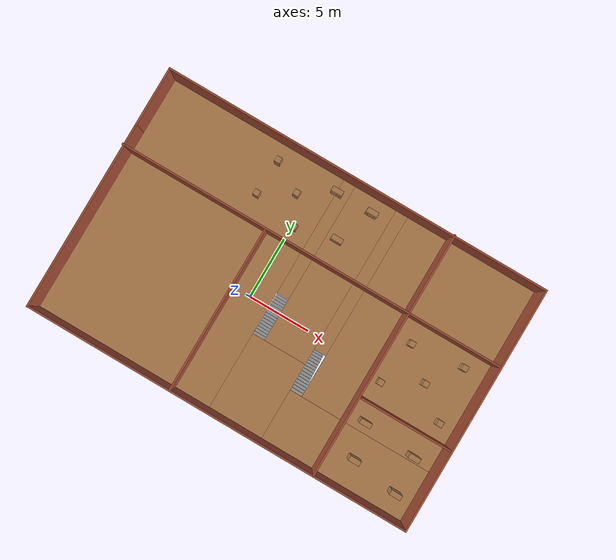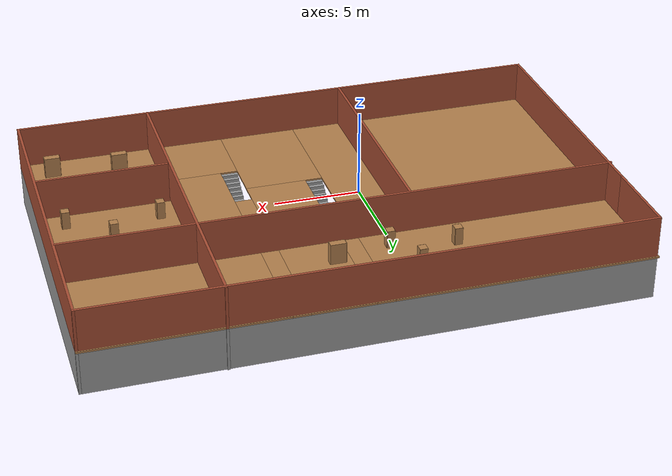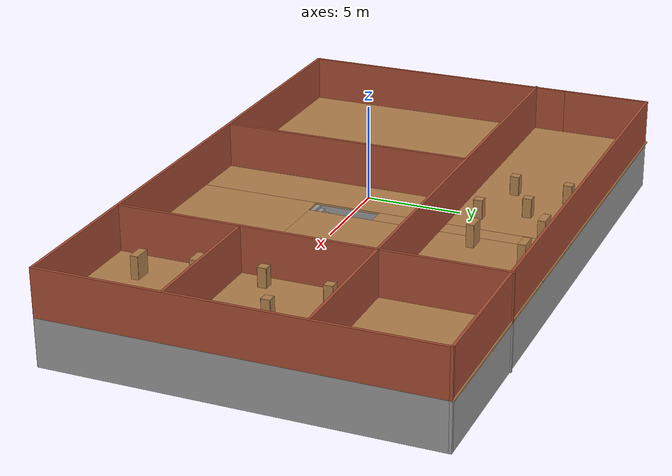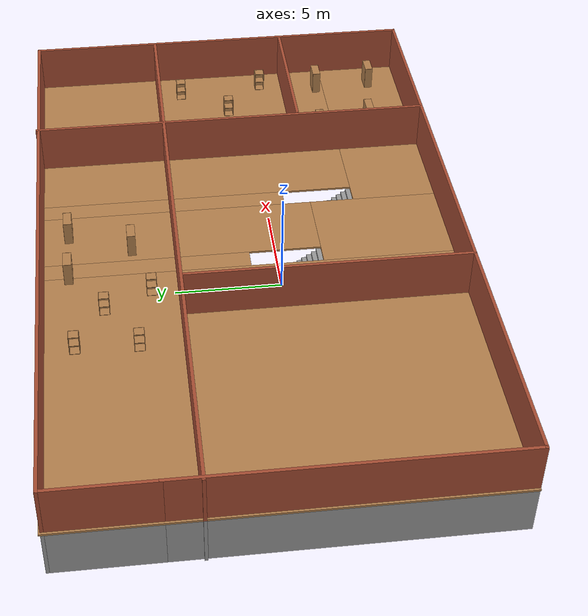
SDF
<sdf version="1.6">
 <world name="default">
  <light name="sun" type="directional">
   <pose>0 0 10 0 -0 0</pose>
   <diffuse>0.8 0.8 0.8 1</diffuse>
   <specular>0.2 0.2 0.2 1</specular>
   <attenuation>
    <range>1000</range>
    <constant>0.9</constant>
    <linear>0.01</linear>
    <quadratic>0.001</quadratic>
   </attenuation>
   <direction>-0.5 0.1 -0.9</direction>
  </light>
  <gravity>0 0 -9.8</gravity>
  <magnetic_field>6e-06 2.3e-05 -4.2e-05</magnetic_field>
  <atmosphere type="adiabatic"/>
  <physics name="default_physics" default="0" type="ode">
   <max_step_size>0.001</max_step_size>
   <real_time_factor>1</real_time_factor>
   <real_time_update_rate>1000</real_time_update_rate>
  </physics>
  <scene><ambient>0.4 0.4 0.4 1</ambient><background>0.7 0.7 0.7 1</background><shadows>1</shadows></scene>
  <audio><device>default</device></audio>
  <spherical_coordinates>
   <surface_model>EARTH_WGS84</surface_model>
   <latitude_deg>0</latitude_deg>
   <longitude_deg>0</longitude_deg>
   <elevation>0</elevation>
   <heading_deg>0</heading_deg>
  </spherical_coordinates>
  <model name="Untitled">
   <pose>2.40942 1.27756 -2.6 0 -0 0</pose>
   <link name="Floor_1">
    <pose>-0 -0 2.5 0 -0 0</pose>
    <visual name="Floor_1_Visual_0">
     <pose>-8.31719 0 0.05 0 -0 0</pose>
     <geometry><box><size>14.9584 20.0724 0.1</size></box></geometry>
     <material>
      <script><uri>file://media/materials/scripts/gazebo.material</uri><name>Gazebo/Wood</name></script>
      <ambient>1 1 1 1</ambient>
     </material>
     <meta><layer>1</layer></meta>
    </visual>
    <collision name="Floor_1_Collision_0">
     <geometry><box><size>14.9584 20.0724 0.1</size></box></geometry>
     <pose>-8.31719 0 0.05 0 -0 0</pose>
    </collision>
    <visual name="Floor_1_Visual_1">
     <pose>1.42625 -6.78262 0.05 0 -0 0</pose>
     <geometry><box><size>4.52845 6.50717 0.1</size></box></geometry>
     <material>
      <script><uri>file://media/materials/scripts/gazebo.material</uri><name>Gazebo/Wood</name></script>
      <ambient>1 1 1 1</ambient>
     </material>
     <meta><layer>1</layer></meta>
    </visual>
    <collision name="Floor_1_Collision_1">
     <geometry><box><size>4.52845 6.50717 0.1</size></box></geometry>
     <pose>1.42625 -6.78262 0.05 0 -0 0</pose>
    </collision>
    <visual name="Floor_1_Visual_2">
     <pose>9.74344 -7.87936 0.05 0 -0 0</pose>
     <geometry><box><size>12.1059 4.3137 0.1</size></box></geometry>
     <material>
      <script><uri>file://media/materials/scripts/gazebo.material</uri><name>Gazebo/Wood</name></script>
      <ambient>1 1 1 1</ambient>
     </material>
     <meta><layer>1</layer></meta>
    </visual>
    <collision name="Floor_1_Collision_2">
     <geometry><box><size>12.1059 4.3137 0.1</size></box></geometry>
     <pose>9.74344 -7.87936 0.05 0 -0 0</pose>
    </collision>
    <visual name="Floor_1_Visual_3">
     <pose>10.2434 2.15685 0.05 0 -0 0</pose>
     <geometry><box><size>11.1059 15.7587 0.1</size></box></geometry>
     <material>
      <script><uri>file://media/materials/scripts/gazebo.material</uri><name>Gazebo/Wood</name></script>
      <ambient>1 1 1 1</ambient>
     </material>
     <meta><layer>1</layer></meta>
    </visual>
    <collision name="Floor_1_Collision_3">
     <geometry><box><size>11.1059 15.7587 0.1</size></box></geometry>
     <pose>10.2434 2.15685 0.05 0 -0 0</pose>
    </collision>
    <visual name="Floor_1_Visual_4">
     <pose>1.92625 3.25358 0.05 0 -0 0</pose>
     <geometry><box><size>3.52845 13.5652 0.1</size></box></geometry>
     <material>
      <script><uri>file://media/materials/scripts/gazebo.material</uri><name>Gazebo/Wood</name></script>
      <ambient>1 1 1 1</ambient>
     </material>
     <meta><layer>1</layer></meta>
    </visual>
    <collision name="Floor_1_Collision_4">
     <geometry><box><size>3.52845 13.5652 0.1</size></box></geometry>
     <pose>1.92625 3.25358 0.05 0 -0 0</pose>
    </collision>
    <visual name="Floor_1_Visual_5">
     <pose>4.19048 3.90685 0.05 0 -0 0</pose>
     <geometry><box><size>1 12.2587 0.1</size></box></geometry>
     <material>
      <script><uri>file://media/materials/scripts/gazebo.material</uri><name>Gazebo/Wood</name></script>
      <ambient>1 1 1 1</ambient>
     </material>
     <meta><layer>1</layer></meta>
    </visual>
    <collision name="Floor_1_Collision_5">
     <geometry><box><size>1 12.2587 0.1</size></box></geometry>
     <pose>4.19048 3.90685 0.05 0 -0 0</pose>
    </collision>
    <visual name="Floor_1_Visual_6">
     <pose>-0.337975 5.00358 0.05 0 -0 0</pose>
     <geometry><box><size>1 10.0652 0.1</size></box></geometry>
     <material>
      <script><uri>file://media/materials/scripts/gazebo.material</uri><name>Gazebo/Wood</name></script>
      <ambient>1 1 1 1</ambient>
     </material>
     <meta><layer>1</layer></meta>
    </visual>
    <collision name="Floor_1_Collision_6">
     <geometry><box><size>1 10.0652 0.1</size></box></geometry>
     <pose>-0.337975 5.00358 0.05 0 -0 0</pose>
    </collision>
   </link>
   <link name="Stairs_2">
    <visual name="Stairs_2_Visual_0">
     <pose>-0.337975 -0.145704 0.083333 0 -0 0</pose>
     <geometry><box><size>1 0.233333 0.166667</size></box></geometry>
     <material>
      <script><uri>file://media/materials/scripts/gazebo.material</uri><name>Gazebo/Grey</name></script>
      <ambient>1 1 1 1</ambient>
     </material>
     <meta><layer>0</layer></meta>
    </visual>
    <collision name="Stairs_2_Collision_0">
     <geometry><box><size>1 0.233333 0.166667</size></box></geometry>
     <pose>-0.337975 -0.145704 0.083333 0 -0 0</pose>
    </collision>
    <visual name="Stairs_2_Visual_1">
     <pose>-0.337975 -0.379037 0.25 0 -0 0</pose>
     <geometry><box><size>1 0.233333 0.166667</size></box></geometry>
     <material>
      <script><uri>file://media/materials/scripts/gazebo.material</uri><name>Gazebo/Grey</name></script>
      <ambient>1 1 1 1</ambient>
     </material>
     <meta><layer>0</layer></meta>
    </visual>
    <collision name="Stairs_2_Collision_1">
     <geometry><box><size>1 0.233333 0.166667</size></box></geometry>
     <pose>-0.337975 -0.379037 0.25 0 -0 0</pose>
    </collision>
    <visual name="Stairs_2_Visual_2">
     <pose>-0.337975 -0.61237 0.416667 0 -0 0</pose>
     <geometry><box><size>1 0.233333 0.166667</size></box></geometry>
     <material>
      <script><uri>file://media/materials/scripts/gazebo.material</uri><name>Gazebo/Grey</name></script>
      <ambient>1 1 1 1</ambient>
     </material>
     <meta><layer>0</layer></meta>
    </visual>
    <collision name="Stairs_2_Collision_2">
     <geometry><box><size>1 0.233333 0.166667</size></box></geometry>
     <pose>-0.337975 -0.61237 0.416667 0 -0 0</pose>
    </collision>
    <visual name="Stairs_2_Visual_3">
     <pose>-0.337975 -0.845704 0.583333 0 -0 0</pose>
     <geometry><box><size>1 0.233333 0.166667</size></box></geometry>
     <material>
      <script><uri>file://media/materials/scripts/gazebo.material</uri><name>Gazebo/Grey</name></script>
      <ambient>1 1 1 1</ambient>
     </material>
     <meta><layer>0</layer></meta>
    </visual>
    <collision name="Stairs_2_Collision_3">
     <geometry><box><size>1 0.233333 0.166667</size></box></geometry>
     <pose>-0.337975 -0.845704 0.583333 0 -0 0</pose>
    </collision>
    <visual name="Stairs_2_Visual_4">
     <pose>-0.337975 -1.07904 0.75 0 -0 0</pose>
     <geometry><box><size>1 0.233333 0.166667</size></box></geometry>
     <material>
      <script><uri>file://media/materials/scripts/gazebo.material</uri><name>Gazebo/Grey</name></script>
      <ambient>1 1 1 1</ambient>
     </material>
     <meta><layer>0</layer></meta>
    </visual>
    <collision name="Stairs_2_Collision_4">
     <geometry><box><size>1 0.233333 0.166667</size></box></geometry>
     <pose>-0.337975 -1.07904 0.75 0 -0 0</pose>
    </collision>
    <visual name="Stairs_2_Visual_5">
     <pose>-0.337975 -1.31237 0.916667 0 -0 0</pose>
     <geometry><box><size>1 0.233333 0.166667</size></box></geometry>
     <material>
      <script><uri>file://media/materials/scripts/gazebo.material</uri><name>Gazebo/Grey</name></script>
      <ambient>1 1 1 1</ambient>
     </material>
     <meta><layer>0</layer></meta>
    </visual>
    <collision name="Stairs_2_Collision_5">
     <geometry><box><size>1 0.233333 0.166667</size></box></geometry>
     <pose>-0.337975 -1.31237 0.916667 0 -0 0</pose>
    </collision>
    <visual name="Stairs_2_Visual_6">
     <pose>-0.337975 -1.5457 1.08333 0 -0 0</pose>
     <geometry><box><size>1 0.233333 0.166667</size></box></geometry>
     <material>
      <script><uri>file://media/materials/scripts/gazebo.material</uri><name>Gazebo/Grey</name></script>
      <ambient>1 1 1 1</ambient>
     </material>
     <meta><layer>0</layer></meta>
    </visual>
    <collision name="Stairs_2_Collision_6">
     <geometry><box><size>1 0.233333 0.166667</size></box></geometry>
     <pose>-0.337975 -1.5457 1.08333 0 -0 0</pose>
    </collision>
    <visual name="Stairs_2_Visual_7">
     <pose>-0.337975 -1.77904 1.25 0 -0 0</pose>
     <geometry><box><size>1 0.233333 0.166667</size></box></geometry>
     <material>
      <script><uri>file://media/materials/scripts/gazebo.material</uri><name>Gazebo/Grey</name></script>
      <ambient>1 1 1 1</ambient>
     </material>
     <meta><layer>0</layer></meta>
    </visual>
    <collision name="Stairs_2_Collision_7">
     <geometry><box><size>1 0.233333 0.166667</size></box></geometry>
     <pose>-0.337975 -1.77904 1.25 0 -0 0</pose>
    </collision>
    <visual name="Stairs_2_Visual_8">
     <pose>-0.337975 -2.01237 1.41667 0 -0 0</pose>
     <geometry><box><size>1 0.233333 0.166667</size></box></geometry>
     <material>
      <script><uri>file://media/materials/scripts/gazebo.material</uri><name>Gazebo/Grey</name></script>
      <ambient>1 1 1 1</ambient>
     </material>
     <meta><layer>0</layer></meta>
    </visual>
    <collision name="Stairs_2_Collision_8">
     <geometry><box><size>1 0.233333 0.166667</size></box></geometry>
     <pose>-0.337975 -2.01237 1.41667 0 -0 0</pose>
    </collision>
    <visual name="Stairs_2_Visual_9">
     <pose>-0.337975 -2.2457 1.58333 0 -0 0</pose>
     <geometry><box><size>1 0.233333 0.166667</size></box></geometry>
     <material>
      <script><uri>file://media/materials/scripts/gazebo.material</uri><name>Gazebo/Grey</name></script>
      <ambient>1 1 1 1</ambient>
     </material>
     <meta><layer>0</layer></meta>
    </visual>
    <collision name="Stairs_2_Collision_9">
     <geometry><box><size>1 0.233333 0.166667</size></box></geometry>
     <pose>-0.337975 -2.2457 1.58333 0 -0 0</pose>
    </collision>
    <visual name="Stairs_2_Visual_10">
     <pose>-0.337975 -2.47904 1.75 0 -0 0</pose>
     <geometry><box><size>1 0.233333 0.166667</size></box></geometry>
     <material>
      <script><uri>file://media/materials/scripts/gazebo.material</uri><name>Gazebo/Grey</name></script>
      <ambient>1 1 1 1</ambient>
     </material>
     <meta><layer>0</layer></meta>
    </visual>
    <collision name="Stairs_2_Collision_10">
     <geometry><box><size>1 0.233333 0.166667</size></box></geometry>
     <pose>-0.337975 -2.47904 1.75 0 -0 0</pose>
    </collision>
    <visual name="Stairs_2_Visual_11">
     <pose>-0.337975 -2.71237 1.91667 0 -0 0</pose>
     <geometry><box><size>1 0.233333 0.166667</size></box></geometry>
     <material>
      <script><uri>file://media/materials/scripts/gazebo.material</uri><name>Gazebo/Grey</name></script>
      <ambient>1 1 1 1</ambient>
     </material>
     <meta><layer>0</layer></meta>
    </visual>
    <collision name="Stairs_2_Collision_11">
     <geometry><box><size>1 0.233333 0.166667</size></box></geometry>
     <pose>-0.337975 -2.71237 1.91667 0 -0 0</pose>
    </collision>
    <visual name="Stairs_2_Visual_12">
     <pose>-0.337975 -2.9457 2.08333 0 -0 0</pose>
     <geometry><box><size>1 0.233333 0.166667</size></box></geometry>
     <material>
      <script><uri>file://media/materials/scripts/gazebo.material</uri><name>Gazebo/Grey</name></script>
      <ambient>1 1 1 1</ambient>
     </material>
     <meta><layer>0</layer></meta>
    </visual>
    <collision name="Stairs_2_Collision_12">
     <geometry><box><size>1 0.233333 0.166667</size></box></geometry>
     <pose>-0.337975 -2.9457 2.08333 0 -0 0</pose>
    </collision>
    <visual name="Stairs_2_Visual_13">
     <pose>-0.337975 -3.17904 2.25 0 -0 0</pose>
     <geometry><box><size>1 0.233333 0.166667</size></box></geometry>
     <material>
      <script><uri>file://media/materials/scripts/gazebo.material</uri><name>Gazebo/Grey</name></script>
      <ambient>1 1 1 1</ambient>
     </material>
     <meta><layer>0</layer></meta>
    </visual>
    <collision name="Stairs_2_Collision_13">
     <geometry><box><size>1 0.233333 0.166667</size></box></geometry>
     <pose>-0.337975 -3.17904 2.25 0 -0 0</pose>
    </collision>
    <visual name="Stairs_2_Visual_14">
     <pose>-0.337975 -3.41237 2.41667 0 -0 0</pose>
     <geometry><box><size>1 0.233333 0.166667</size></box></geometry>
     <material>
      <script><uri>file://media/materials/scripts/gazebo.material</uri><name>Gazebo/Grey</name></script>
      <ambient>1 1 1 1</ambient>
     </material>
     <meta><layer>0</layer></meta>
    </visual>
    <collision name="Stairs_2_Collision_14">
     <geometry><box><size>1 0.233333 0.166667</size></box></geometry>
     <pose>-0.337975 -3.41237 2.41667 0 -0 0</pose>
    </collision>
   </link>
   <link name="Stairs_3">
    <visual name="Stairs_3_Visual_0">
     <pose>4.19048 -2.33917 0.083333 0 -0 0</pose>
     <geometry><box><size>1 0.233333 0.166667</size></box></geometry>
     <material>
      <script><uri>file://media/materials/scripts/gazebo.material</uri><name>Gazebo/Grey</name></script>
      <ambient>1 1 1 1</ambient>
     </material>
     <meta><layer>0</layer></meta>
    </visual>
    <collision name="Stairs_3_Collision_0">
     <geometry><box><size>1 0.233333 0.166667</size></box></geometry>
     <pose>4.19048 -2.33917 0.083333 0 -0 0</pose>
    </collision>
    <visual name="Stairs_3_Visual_1">
     <pose>4.19048 -2.57251 0.25 0 -0 0</pose>
     <geometry><box><size>1 0.233333 0.166667</size></box></geometry>
     <material>
      <script><uri>file://media/materials/scripts/gazebo.material</uri><name>Gazebo/Grey</name></script>
      <ambient>1 1 1 1</ambient>
     </material>
     <meta><layer>0</layer></meta>
    </visual>
    <collision name="Stairs_3_Collision_1">
     <geometry><box><size>1 0.233333 0.166667</size></box></geometry>
     <pose>4.19048 -2.57251 0.25 0 -0 0</pose>
    </collision>
    <visual name="Stairs_3_Visual_2">
     <pose>4.19048 -2.80584 0.416667 0 -0 0</pose>
     <geometry><box><size>1 0.233333 0.166667</size></box></geometry>
     <material>
      <script><uri>file://media/materials/scripts/gazebo.material</uri><name>Gazebo/Grey</name></script>
      <ambient>1 1 1 1</ambient>
     </material>
     <meta><layer>0</layer></meta>
    </visual>
    <collision name="Stairs_3_Collision_2">
     <geometry><box><size>1 0.233333 0.166667</size></box></geometry>
     <pose>4.19048 -2.80584 0.416667 0 -0 0</pose>
    </collision>
    <visual name="Stairs_3_Visual_3">
     <pose>4.19048 -3.03917 0.583333 0 -0 0</pose>
     <geometry><box><size>1 0.233333 0.166667</size></box></geometry>
     <material>
      <script><uri>file://media/materials/scripts/gazebo.material</uri><name>Gazebo/Grey</name></script>
      <ambient>1 1 1 1</ambient>
     </material>
     <meta><layer>0</layer></meta>
    </visual>
    <collision name="Stairs_3_Collision_3">
     <geometry><box><size>1 0.233333 0.166667</size></box></geometry>
     <pose>4.19048 -3.03917 0.583333 0 -0 0</pose>
    </collision>
    <visual name="Stairs_3_Visual_4">
     <pose>4.19048 -3.27251 0.75 0 -0 0</pose>
     <geometry><box><size>1 0.233333 0.166667</size></box></geometry>
     <material>
      <script><uri>file://media/materials/scripts/gazebo.material</uri><name>Gazebo/Grey</name></script>
      <ambient>1 1 1 1</ambient>
     </material>
     <meta><layer>0</layer></meta>
    </visual>
    <collision name="Stairs_3_Collision_4">
     <geometry><box><size>1 0.233333 0.166667</size></box></geometry>
     <pose>4.19048 -3.27251 0.75 0 -0 0</pose>
    </collision>
    <visual name="Stairs_3_Visual_5">
     <pose>4.19048 -3.50584 0.916667 0 -0 0</pose>
     <geometry><box><size>1 0.233333 0.166667</size></box></geometry>
     <material>
      <script><uri>file://media/materials/scripts/gazebo.material</uri><name>Gazebo/Grey</name></script>
      <ambient>1 1 1 1</ambient>
     </material>
     <meta><layer>0</layer></meta>
    </visual>
    <collision name="Stairs_3_Collision_5">
     <geometry><box><size>1 0.233333 0.166667</size></box></geometry>
     <pose>4.19048 -3.50584 0.916667 0 -0 0</pose>
    </collision>
    <visual name="Stairs_3_Visual_6">
     <pose>4.19048 -3.73917 1.08333 0 -0 0</pose>
     <geometry><box><size>1 0.233333 0.166667</size></box></geometry>
     <material>
      <script><uri>file://media/materials/scripts/gazebo.material</uri><name>Gazebo/Grey</name></script>
      <ambient>1 1 1 1</ambient>
     </material>
     <meta><layer>0</layer></meta>
    </visual>
    <collision name="Stairs_3_Collision_6">
     <geometry><box><size>1 0.233333 0.166667</size></box></geometry>
     <pose>4.19048 -3.73917 1.08333 0 -0 0</pose>
    </collision>
    <visual name="Stairs_3_Visual_7">
     <pose>4.19048 -3.97251 1.25 0 -0 0</pose>
     <geometry><box><size>1 0.233333 0.166667</size></box></geometry>
     <material>
      <script><uri>file://media/materials/scripts/gazebo.material</uri><name>Gazebo/Grey</name></script>
      <ambient>1 1 1 1</ambient>
     </material>
     <meta><layer>0</layer></meta>
    </visual>
    <collision name="Stairs_3_Collision_7">
     <geometry><box><size>1 0.233333 0.166667</size></box></geometry>
     <pose>4.19048 -3.97251 1.25 0 -0 0</pose>
    </collision>
    <visual name="Stairs_3_Visual_8">
     <pose>4.19048 -4.20584 1.41667 0 -0 0</pose>
     <geometry><box><size>1 0.233333 0.166667</size></box></geometry>
     <material>
      <script><uri>file://media/materials/scripts/gazebo.material</uri><name>Gazebo/Grey</name></script>
      <ambient>1 1 1 1</ambient>
     </material>
     <meta><layer>0</layer></meta>
    </visual>
    <collision name="Stairs_3_Collision_8">
     <geometry><box><size>1 0.233333 0.166667</size></box></geometry>
     <pose>4.19048 -4.20584 1.41667 0 -0 0</pose>
    </collision>
    <visual name="Stairs_3_Visual_9">
     <pose>4.19048 -4.43917 1.58333 0 -0 0</pose>
     <geometry><box><size>1 0.233333 0.166667</size></box></geometry>
     <material>
      <script><uri>file://media/materials/scripts/gazebo.material</uri><name>Gazebo/Grey</name></script>
      <ambient>1 1 1 1</ambient>
     </material>
     <meta><layer>0</layer></meta>
    </visual>
    <collision name="Stairs_3_Collision_9">
     <geometry><box><size>1 0.233333 0.166667</size></box></geometry>
     <pose>4.19048 -4.43917 1.58333 0 -0 0</pose>
    </collision>
    <visual name="Stairs_3_Visual_10">
     <pose>4.19048 -4.67251 1.75 0 -0 0</pose>
     <geometry><box><size>1 0.233333 0.166667</size></box></geometry>
     <material>
      <script><uri>file://media/materials/scripts/gazebo.material</uri><name>Gazebo/Grey</name></script>
      <ambient>1 1 1 1</ambient>
     </material>
     <meta><layer>0</layer></meta>
    </visual>
    <collision name="Stairs_3_Collision_10">
     <geometry><box><size>1 0.233333 0.166667</size></box></geometry>
     <pose>4.19048 -4.67251 1.75 0 -0 0</pose>
    </collision>
    <visual name="Stairs_3_Visual_11">
     <pose>4.19048 -4.90584 1.91667 0 -0 0</pose>
     <geometry><box><size>1 0.233333 0.166667</size></box></geometry>
     <material>
      <script><uri>file://media/materials/scripts/gazebo.material</uri><name>Gazebo/Grey</name></script>
      <ambient>1 1 1 1</ambient>
     </material>
     <meta><layer>0</layer></meta>
    </visual>
    <collision name="Stairs_3_Collision_11">
     <geometry><box><size>1 0.233333 0.166667</size></box></geometry>
     <pose>4.19048 -4.90584 1.91667 0 -0 0</pose>
    </collision>
    <visual name="Stairs_3_Visual_12">
     <pose>4.19048 -5.13917 2.08333 0 -0 0</pose>
     <geometry><box><size>1 0.233333 0.166667</size></box></geometry>
     <material>
      <script><uri>file://media/materials/scripts/gazebo.material</uri><name>Gazebo/Grey</name></script>
      <ambient>1 1 1 1</ambient>
     </material>
     <meta><layer>0</layer></meta>
    </visual>
    <collision name="Stairs_3_Collision_12">
     <geometry><box><size>1 0.233333 0.166667</size></box></geometry>
     <pose>4.19048 -5.13917 2.08333 0 -0 0</pose>
    </collision>
    <visual name="Stairs_3_Visual_13">
     <pose>4.19048 -5.37251 2.25 0 -0 0</pose>
     <geometry><box><size>1 0.233333 0.166667</size></box></geometry>
     <material>
      <script><uri>file://media/materials/scripts/gazebo.material</uri><name>Gazebo/Grey</name></script>
      <ambient>1 1 1 1</ambient>
     </material>
     <meta><layer>0</layer></meta>
    </visual>
    <collision name="Stairs_3_Collision_13">
     <geometry><box><size>1 0.233333 0.166667</size></box></geometry>
     <pose>4.19048 -5.37251 2.25 0 -0 0</pose>
    </collision>
    <visual name="Stairs_3_Visual_14">
     <pose>4.19048 -5.60584 2.41667 0 -0 0</pose>
     <geometry><box><size>1 0.233333 0.166667</size></box></geometry>
     <material>
      <script><uri>file://media/materials/scripts/gazebo.material</uri><name>Gazebo/Grey</name></script>
      <ambient>1 1 1 1</ambient>
     </material>
     <meta><layer>0</layer></meta>
    </visual>
    <collision name="Stairs_3_Collision_14">
     <geometry><box><size>1 0.233333 0.166667</size></box></geometry>
     <pose>4.19048 -5.60584 2.41667 0 -0 0</pose>
    </collision>
   </link>
   <link name="Wall_1">
    <collision name="Wall_1_Collision">
     <geometry><box><size>15.25 0.15 2.5</size></box></geometry>
     <pose>0 0 1.25 0 -0 0</pose>
    </collision>
    <visual name="Wall_1_Visual">
     <pose>0 0 1.25 0 -0 0</pose>
     <geometry><box><size>15.25 0.15 2.5</size></box></geometry>
     <material>
      <script><uri>file://media/materials/scripts/gazebo.material</uri><name>Gazebo/Grey</name></script>
      <ambient>1 1 1 1</ambient>
     </material>
     <meta><layer>0</layer></meta>
    </visual>
    <pose>-15.6286 -2.4112 0 0 -0 -1.5708</pose>
   </link>
   <link name="Wall_11">
    <collision name="Wall_11_Collision">
     <geometry><box><size>20 0.15 2.5</size></box></geometry>
     <pose>0 0 1.25 0 -0 0</pose>
    </collision>
    <visual name="Wall_11_Visual">
     <pose>0 0 1.25 0 -0 0</pose>
     <geometry><box><size>20 0.15 2.5</size></box></geometry>
     <material>
      <script><uri>file://media/materials/scripts/gazebo.material</uri><name>Gazebo/Grey</name></script>
      <ambient>1 1 1 1</ambient>
     </material>
     <meta><layer>0</layer></meta>
    </visual>
    <pose>8.08989 0.036204 0 0 -0 -1.5708</pose>
   </link>
   <link name="Wall_13">
    <collision name="Wall_13_Collision">
     <geometry><box><size>7.5 0.15 2.5</size></box></geometry>
     <pose>0 0 1.25 0 -0 0</pose>
    </collision>
    <visual name="Wall_13_Visual">
     <pose>0 0 1.25 0 -0 0</pose>
     <geometry><box><size>7.5 0.15 2.5</size></box></geometry>
     <material>
      <script><uri>file://media/materials/scripts/gazebo.material</uri><name>Gazebo/Grey</name></script>
      <ambient>1 1 1 1</ambient>
     </material>
     <meta><layer>0</layer></meta>
    </visual>
    <pose>11.9536 -3.45187 0 0 -0 0</pose>
   </link>
   <link name="Wall_16">
    <collision name="Wall_16_Collision">
     <geometry><box><size>31.5 0.15 2.5</size></box></geometry>
     <pose>0 0 1.25 0 -0 0</pose>
    </collision>
    <visual name="Wall_16_Visual">
     <pose>0 0 1.25 0 -0 0</pose>
     <geometry><box><size>31.5 0.15 2.5</size></box></geometry>
     <material>
      <script><uri>file://media/materials/scripts/gazebo.material</uri><name>Gazebo/Grey</name></script>
      <ambient>1 1 1 1</ambient>
     </material>
     <meta><layer>0</layer></meta>
    </visual>
    <pose>-0.0464 3.50078 0 0 -0 0</pose>
   </link>
   <link name="Wall_2">
    <collision name="Wall_2_Collision">
     <geometry><box><size>31.5 0.15 2.5</size></box></geometry>
     <pose>0 0 1.25 0 -0 0</pose>
    </collision>
    <visual name="Wall_2_Visual">
     <pose>0 0 1.25 0 -0 0</pose>
     <geometry><box><size>31.5 0.15 2.5</size></box></geometry>
     <material>
      <script><uri>file://media/materials/scripts/gazebo.material</uri><name>Gazebo/Grey</name></script>
      <ambient>1 1 1 1</ambient>
     </material>
     <meta><layer>0</layer></meta>
    </visual>
    <pose>0.046399 -9.9612 0 0 -0 0</pose>
   </link>
   <link name="Wall_3">
    <collision name="Wall_3_Collision">
     <geometry><box><size>20 0.15 2.5</size></box></geometry>
     <pose>0 0 1.25 0 -0 0</pose>
    </collision>
    <visual name="Wall_3_Visual">
     <pose>0 0 1.25 0 -0 0</pose>
     <geometry><box><size>20 0.15 2.5</size></box></geometry>
     <material>
      <script><uri>file://media/materials/scripts/gazebo.material</uri><name>Gazebo/Grey</name></script>
      <ambient>1 1 1 1</ambient>
     </material>
     <meta><layer>0</layer></meta>
    </visual>
    <pose>15.7214 -0.036205 0 0 -0 1.5708</pose>
   </link>
   <link name="Wall_32">
    <collision name="Wall_32_Collision">
     <geometry><box><size>15.25 0.15 2.5</size></box></geometry>
     <pose>0 0 1.25 0 -0 0</pose>
    </collision>
    <visual name="Wall_32_Visual">
     <pose>0 0 1.25 0 -0 0</pose>
     <geometry><box><size>15.25 0.15 2.5</size></box></geometry>
     <material>
      <script><uri>file://media/materials/scripts/gazebo.material</uri><name>Gazebo/Bricks</name></script>
      <ambient>1 1 1 1</ambient>
     </material>
     <meta><layer>1</layer></meta>
    </visual>
    <pose>-15.6286 -2.4112 2.5 0 -0 -1.5708</pose>
   </link>
   <link name="Wall_33">
    <collision name="Wall_33_Collision">
     <geometry><box><size>31.5 0.15 2.5</size></box></geometry>
     <pose>0 0 1.25 0 -0 0</pose>
    </collision>
    <visual name="Wall_33_Visual">
     <pose>0 0 1.25 0 -0 0</pose>
     <geometry><box><size>31.5 0.15 2.5</size></box></geometry>
     <material>
      <script><uri>file://media/materials/scripts/gazebo.material</uri><name>Gazebo/Bricks</name></script>
      <ambient>1 1 1 1</ambient>
     </material>
     <meta><layer>1</layer></meta>
    </visual>
    <pose>0.046399 -9.9612 2.5 0 -0 0</pose>
   </link>
   <link name="Wall_34">
    <collision name="Wall_34_Collision">
     <geometry><box><size>20 0.15 2.5</size></box></geometry>
     <pose>0 0 1.25 0 -0 0</pose>
    </collision>
    <visual name="Wall_34_Visual">
     <pose>0 0 1.25 0 -0 0</pose>
     <geometry><box><size>20 0.15 2.5</size></box></geometry>
     <material>
      <script><uri>file://media/materials/scripts/gazebo.material</uri><name>Gazebo/Bricks</name></script>
      <ambient>1 1 1 1</ambient>
     </material>
     <meta><layer>1</layer></meta>
    </visual>
    <pose>15.7214 -0.036205 2.5 0 -0 1.5708</pose>
   </link>
   <link name="Wall_35">
    <collision name="Wall_35_Collision">
     <geometry><box><size>31.5 0.15 2.5</size></box></geometry>
     <pose>0 0 1.25 0 -0 0</pose>
    </collision>
    <visual name="Wall_35_Visual">
     <pose>0 0 1.25 0 -0 0</pose>
     <geometry><box><size>31.5 0.15 2.5</size></box></geometry>
     <material>
      <script><uri>file://media/materials/scripts/gazebo.material</uri><name>Gazebo/Bricks</name></script>
      <ambient>1 1 1 1</ambient>
     </material>
     <meta><layer>1</layer></meta>
    </visual>
    <pose>0.046399 9.8888 2.5 0 -0 3.14159</pose>
   </link>
   <link name="Wall_36">
    <collision name="Wall_36_Collision">
     <geometry><box><size>4.9 0.15 2.5</size></box></geometry>
     <pose>0 0 1.25 0 -0 0</pose>
    </collision>
    <visual name="Wall_36_Visual">
     <pose>0 0 1.25 0 -0 0</pose>
     <geometry><box><size>4.9 0.15 2.5</size></box></geometry>
     <material>
      <script><uri>file://media/materials/scripts/gazebo.material</uri><name>Gazebo/Bricks</name></script>
      <ambient>1 1 1 1</ambient>
     </material>
     <meta><layer>1</layer></meta>
    </visual>
    <pose>-15.6286 7.51379 2.5 0 -0 -1.5708</pose>
   </link>
   <link name="Wall_37">
    <collision name="Wall_37_Collision">
     <geometry><box><size>13.5 0.15 2.5</size></box></geometry>
     <pose>0 0 1.25 0 -0 0</pose>
    </collision>
    <visual name="Wall_37_Visual">
     <pose>0 0 1.25 0 -0 0</pose>
     <geometry><box><size>13.5 0.15 2.5</size></box></geometry>
     <material>
      <script><uri>file://media/materials/scripts/gazebo.material</uri><name>Gazebo/Bricks</name></script>
      <ambient>1 1 1 1</ambient>
     </material>
     <meta><layer>1</layer></meta>
    </visual>
    <pose>-3.81883 -3.28455 2.5 0 -0 -1.5708</pose>
   </link>
   <link name="Wall_38">
    <collision name="Wall_38_Collision">
     <geometry><box><size>20 0.15 2.5</size></box></geometry>
     <pose>0 0 1.25 0 -0 0</pose>
    </collision>
    <visual name="Wall_38_Visual">
     <pose>0 0 1.25 0 -0 0</pose>
     <geometry><box><size>20 0.15 2.5</size></box></geometry>
     <material>
      <script><uri>file://media/materials/scripts/gazebo.material</uri><name>Gazebo/Bricks</name></script>
      <ambient>1 1 1 1</ambient>
     </material>
     <meta><layer>1</layer></meta>
    </visual>
    <pose>8.08989 0.036204 2.5 0 -0 -1.5708</pose>
   </link>
   <link name="Wall_39">
    <collision name="Wall_39_Collision">
     <geometry><box><size>7.5 0.15 2.5</size></box></geometry>
     <pose>0 0 1.25 0 -0 0</pose>
    </collision>
    <visual name="Wall_39_Visual">
     <pose>0 0 1.25 0 -0 0</pose>
     <geometry><box><size>7.5 0.15 2.5</size></box></geometry>
     <material>
      <script><uri>file://media/materials/scripts/gazebo.material</uri><name>Gazebo/Bricks</name></script>
      <ambient>1 1 1 1</ambient>
     </material>
     <meta><layer>1</layer></meta>
    </visual>
    <pose>11.9536 -3.45187 2.5 0 -0 0</pose>
   </link>
   <link name="Wall_4">
    <collision name="Wall_4_Collision">
     <geometry><box><size>31.5 0.15 2.5</size></box></geometry>
     <pose>0 0 1.25 0 -0 0</pose>
    </collision>
    <visual name="Wall_4_Visual">
     <pose>0 0 1.25 0 -0 0</pose>
     <geometry><box><size>31.5 0.15 2.5</size></box></geometry>
     <material>
      <script><uri>file://media/materials/scripts/gazebo.material</uri><name>Gazebo/Grey</name></script>
      <ambient>1 1 1 1</ambient>
     </material>
     <meta><layer>0</layer></meta>
    </visual>
    <pose>0.046399 9.88879 0 0 -0 3.14159</pose>
   </link>
   <link name="Wall_40">
    <collision name="Wall_40_Collision">
     <geometry><box><size>31.5 0.15 2.5</size></box></geometry>
     <pose>0 0 1.25 0 -0 0</pose>
    </collision>
    <visual name="Wall_40_Visual">
     <pose>0 0 1.25 0 -0 0</pose>
     <geometry><box><size>31.5 0.15 2.5</size></box></geometry>
     <material>
      <script><uri>file://media/materials/scripts/gazebo.material</uri><name>Gazebo/Bricks</name></script>
      <ambient>1 1 1 1</ambient>
     </material>
     <meta><layer>1</layer></meta>
    </visual>
    <pose>-0.0464 3.50078 2.5 0 -0 0</pose>
   </link>
   <link name="Wall_5">
    <collision name="Wall_5_Collision">
     <geometry><box><size>4.9 0.15 2.5</size></box></geometry>
     <pose>0 0 1.25 0 -0 0</pose>
    </collision>
    <visual name="Wall_5_Visual">
     <pose>0 0 1.25 0 -0 0</pose>
     <geometry><box><size>4.9 0.15 2.5</size></box></geometry>
     <material>
      <script><uri>file://media/materials/scripts/gazebo.material</uri><name>Gazebo/Grey</name></script>
      <ambient>1 1 1 1</ambient>
     </material>
     <meta><layer>0</layer></meta>
    </visual>
    <pose>-15.6286 7.51379 0 0 -0 -1.5708</pose>
   </link>
   <link name="Wall_9">
    <collision name="Wall_9_Collision">
     <geometry><box><size>13.5 0.15 2.5</size></box></geometry>
     <pose>0 0 1.25 0 -0 0</pose>
    </collision>
    <visual name="Wall_9_Visual">
     <pose>0 0 1.25 0 -0 0</pose>
     <geometry><box><size>13.5 0.15 2.5</size></box></geometry>
     <material>
      <script><uri>file://media/materials/scripts/gazebo.material</uri><name>Gazebo/Grey</name></script>
      <ambient>1 1 1 1</ambient>
     </material>
     <meta><layer>0</layer></meta>
    </visual>
    <pose>-3.81883 -3.28455 0 0 -0 -1.5708</pose>
   </link>
   <static>1</static>
  </model>
  <model name="bookshelf">
   <static>1</static>
   <link name="link">
    <inertial><mass>1</mass></inertial>
    <collision name="back">
     <pose>0 0.005 0.6 0 -0 0</pose>
     <geometry><box><size>0.9 0.01 1.2</size></box></geometry>
    </collision>
    <visual name="visual1">
     <pose>0 0.005 0.6 0 -0 0</pose>
     <geometry><box><size>0.9 0.01 1.2</size></box></geometry>
     <material>
      <script><uri>file://media/materials/scripts/gazebo.material</uri><name>Gazebo/Wood</name></script>
     </material>
    </visual>
    <collision name="left_side">
     <pose>0.45 -0.195 0.6 0 -0 0</pose>
     <geometry><box><size>0.02 0.4 1.2</size></box></geometry>
    </collision>
    <visual name="visual2">
     <pose>0.45 -0.195 0.6 0 -0 0</pose>
     <geometry><box><size>0.02 0.4 1.2</size></box></geometry>
     <material>
      <script><uri>file://media/materials/scripts/gazebo.material</uri><name>Gazebo/Wood</name></script>
     </material>
    </visual>
    <collision name="right_side">
     <pose>-0.45 -0.195 0.6 0 -0 0</pose>
     <geometry><box><size>0.02 0.4 1.2</size></box></geometry>
    </collision>
    <visual name="visual3">
     <pose>-0.45 -0.195 0.6 0 -0 0</pose>
     <geometry><box><size>0.02 0.4 1.2</size></box></geometry>
     <material>
      <script><uri>file://media/materials/scripts/gazebo.material</uri><name>Gazebo/Wood</name></script>
     </material>
    </visual>
    <collision name="bottom">
     <pose>0 -0.195 0.03 0 -0 0</pose>
     <geometry><box><size>0.88 0.4 0.06</size></box></geometry>
    </collision>
    <visual name="visual4">
     <pose>0 -0.195 0.03 0 -0 0</pose>
     <geometry><box><size>0.88 0.4 0.06</size></box></geometry>
     <material>
      <script><uri>file://media/materials/scripts/gazebo.material</uri><name>Gazebo/Wood</name></script>
     </material>
    </visual>
    <collision name="top">
     <pose>0 -0.195 1.19 0 -0 0</pose>
     <geometry><box><size>0.88 0.4 0.02</size></box></geometry>
    </collision>
    <visual name="visual5">
     <pose>0 -0.195 1.19 0 -0 0</pose>
     <geometry><box><size>0.88 0.4 0.02</size></box></geometry>
     <material>
      <script><uri>file://media/materials/scripts/gazebo.material</uri><name>Gazebo/Wood</name></script>
     </material>
    </visual>
    <collision name="low_shelf">
     <pose>0 -0.195 0.43 0 -0 0</pose>
     <geometry><box><size>0.88 0.4 0.02</size></box></geometry>
    </collision>
    <visual name="visual6">
     <pose>0 -0.195 0.43 0 -0 0</pose>
     <geometry><box><size>0.88 0.4 0.02</size></box></geometry>
     <material>
      <script><uri>file://media/materials/scripts/gazebo.material</uri><name>Gazebo/Wood</name></script>
     </material>
    </visual>
    <collision name="high_shelf">
     <pose>0 -0.195 0.8 0 -0 0</pose>
     <geometry><box><size>0.88 0.4 0.02</size></box></geometry>
    </collision>
    <visual name="visual7">
     <pose>0 -0.195 0.8 0 -0 0</pose>
     <geometry><box><size>0.88 0.4 0.02</size></box></geometry>
     <material>
      <script><uri>file://media/materials/scripts/gazebo.material</uri><name>Gazebo/Wood</name></script>
     </material>
    </visual>
   </link>
   <pose>12.0281 -3.44809 0 0 -0 0</pose>
  </model>
  <model name="bookshelf_clone">
   <static>1</static>
   <link name="link">
    <inertial><mass>1</mass></inertial>
    <collision name="back">
     <pose>0 0.005 0.6 0 -0 0</pose>
     <geometry><box><size>0.9 0.01 1.2</size></box></geometry>
    </collision>
    <visual name="visual1">
     <pose>0 0.005 0.6 0 -0 0</pose>
     <geometry><box><size>0.9 0.01 1.2</size></box></geometry>
     <material>
      <script><uri>file://media/materials/scripts/gazebo.material</uri><name>Gazebo/Wood</name></script>
     </material>
    </visual>
    <collision name="left_side">
     <pose>0.45 -0.195 0.6 0 -0 0</pose>
     <geometry><box><size>0.02 0.4 1.2</size></box></geometry>
    </collision>
    <visual name="visual2">
     <pose>0.45 -0.195 0.6 0 -0 0</pose>
     <geometry><box><size>0.02 0.4 1.2</size></box></geometry>
     <material>
      <script><uri>file://media/materials/scripts/gazebo.material</uri><name>Gazebo/Wood</name></script>
     </material>
    </visual>
    <collision name="right_side">
     <pose>-0.45 -0.195 0.6 0 -0 0</pose>
     <geometry><box><size>0.02 0.4 1.2</size></box></geometry>
    </collision>
    <visual name="visual3">
     <pose>-0.45 -0.195 0.6 0 -0 0</pose>
     <geometry><box><size>0.02 0.4 1.2</size></box></geometry>
     <material>
      <script><uri>file://media/materials/scripts/gazebo.material</uri><name>Gazebo/Wood</name></script>
     </material>
    </visual>
    <collision name="bottom">
     <pose>0 -0.195 0.03 0 -0 0</pose>
     <geometry><box><size>0.88 0.4 0.06</size></box></geometry>
    </collision>
    <visual name="visual4">
     <pose>0 -0.195 0.03 0 -0 0</pose>
     <geometry><box><size>0.88 0.4 0.06</size></box></geometry>
     <material>
      <script><uri>file://media/materials/scripts/gazebo.material</uri><name>Gazebo/Wood</name></script>
     </material>
    </visual>
    <collision name="top">
     <pose>0 -0.195 1.19 0 -0 0</pose>
     <geometry><box><size>0.88 0.4 0.02</size></box></geometry>
    </collision>
    <visual name="visual5">
     <pose>0 -0.195 1.19 0 -0 0</pose>
     <geometry><box><size>0.88 0.4 0.02</size></box></geometry>
     <material>
      <script><uri>file://media/materials/scripts/gazebo.material</uri><name>Gazebo/Wood</name></script>
     </material>
    </visual>
    <collision name="low_shelf">
     <pose>0 -0.195 0.43 0 -0 0</pose>
     <geometry><box><size>0.88 0.4 0.02</size></box></geometry>
    </collision>
    <visual name="visual6">
     <pose>0 -0.195 0.43 0 -0 0</pose>
     <geometry><box><size>0.88 0.4 0.02</size></box></geometry>
     <material>
      <script><uri>file://media/materials/scripts/gazebo.material</uri><name>Gazebo/Wood</name></script>
     </material>
    </visual>
    <collision name="high_shelf">
     <pose>0 -0.195 0.8 0 -0 0</pose>
     <geometry><box><size>0.88 0.4 0.02</size></box></geometry>
    </collision>
    <visual name="visual7">
     <pose>0 -0.195 0.8 0 -0 0</pose>
     <geometry><box><size>0.88 0.4 0.02</size></box></geometry>
     <material>
      <script><uri>file://media/materials/scripts/gazebo.material</uri><name>Gazebo/Wood</name></script>
     </material>
    </visual>
   </link>
   <pose>12.7142 -6.19402 0 0 -0 0</pose>
  </model>
  <model name="bookshelf_clone_0">
   <static>1</static>
   <link name="link">
    <inertial><mass>1</mass></inertial>
    <collision name="back">
     <pose>0 0.005 0.6 0 -0 0</pose>
     <geometry><box><size>0.9 0.01 1.2</size></box></geometry>
    </collision>
    <visual name="visual1">
     <pose>0 0.005 0.6 0 -0 0</pose>
     <geometry><box><size>0.9 0.01 1.2</size></box></geometry>
     <material>
      <script><uri>file://media/materials/scripts/gazebo.material</uri><name>Gazebo/Wood</name></script>
     </material>
    </visual>
    <collision name="left_side">
     <pose>0.45 -0.195 0.6 0 -0 0</pose>
     <geometry><box><size>0.02 0.4 1.2</size></box></geometry>
    </collision>
    <visual name="visual2">
     <pose>0.45 -0.195 0.6 0 -0 0</pose>
     <geometry><box><size>0.02 0.4 1.2</size></box></geometry>
     <material>
      <script><uri>file://media/materials/scripts/gazebo.material</uri><name>Gazebo/Wood</name></script>
     </material>
    </visual>
    <collision name="right_side">
     <pose>-0.45 -0.195 0.6 0 -0 0</pose>
     <geometry><box><size>0.02 0.4 1.2</size></box></geometry>
    </collision>
    <visual name="visual3">
     <pose>-0.45 -0.195 0.6 0 -0 0</pose>
     <geometry><box><size>0.02 0.4 1.2</size></box></geometry>
     <material>
      <script><uri>file://media/materials/scripts/gazebo.material</uri><name>Gazebo/Wood</name></script>
     </material>
    </visual>
    <collision name="bottom">
     <pose>0 -0.195 0.03 0 -0 0</pose>
     <geometry><box><size>0.88 0.4 0.06</size></box></geometry>
    </collision>
    <visual name="visual4">
     <pose>0 -0.195 0.03 0 -0 0</pose>
     <geometry><box><size>0.88 0.4 0.06</size></box></geometry>
     <material>
      <script><uri>file://media/materials/scripts/gazebo.material</uri><name>Gazebo/Wood</name></script>
     </material>
    </visual>
    <collision name="top">
     <pose>0 -0.195 1.19 0 -0 0</pose>
     <geometry><box><size>0.88 0.4 0.02</size></box></geometry>
    </collision>
    <visual name="visual5">
     <pose>0 -0.195 1.19 0 -0 0</pose>
     <geometry><box><size>0.88 0.4 0.02</size></box></geometry>
     <material>
      <script><uri>file://media/materials/scripts/gazebo.material</uri><name>Gazebo/Wood</name></script>
     </material>
    </visual>
    <collision name="low_shelf">
     <pose>0 -0.195 0.43 0 -0 0</pose>
     <geometry><box><size>0.88 0.4 0.02</size></box></geometry>
    </collision>
    <visual name="visual6">
     <pose>0 -0.195 0.43 0 -0 0</pose>
     <geometry><box><size>0.88 0.4 0.02</size></box></geometry>
     <material>
      <script><uri>file://media/materials/scripts/gazebo.material</uri><name>Gazebo/Wood</name></script>
     </material>
    </visual>
    <collision name="high_shelf">
     <pose>0 -0.195 0.8 0 -0 0</pose>
     <geometry><box><size>0.88 0.4 0.02</size></box></geometry>
    </collision>
    <visual name="visual7">
     <pose>0 -0.195 0.8 0 -0 0</pose>
     <geometry><box><size>0.88 0.4 0.02</size></box></geometry>
     <material>
      <script><uri>file://media/materials/scripts/gazebo.material</uri><name>Gazebo/Wood</name></script>
     </material>
    </visual>
   </link>
   <pose>16.3675 -3.8301 0 0 -0 0</pose>
  </model>
  <model name="bookshelf_clone_1">
   <static>1</static>
   <link name="link">
    <inertial><mass>1</mass></inertial>
    <collision name="back">
     <pose>0 0.005 0.6 0 -0 0</pose>
     <geometry><box><size>0.9 0.01 1.2</size></box></geometry>
    </collision>
    <visual name="visual1">
     <pose>0 0.005 0.6 0 -0 0</pose>
     <geometry><box><size>0.9 0.01 1.2</size></box></geometry>
     <material>
      <script><uri>file://media/materials/scripts/gazebo.material</uri><name>Gazebo/Wood</name></script>
     </material>
    </visual>
    <collision name="left_side">
     <pose>0.45 -0.195 0.6 0 -0 0</pose>
     <geometry><box><size>0.02 0.4 1.2</size></box></geometry>
    </collision>
    <visual name="visual2">
     <pose>0.45 -0.195 0.6 0 -0 0</pose>
     <geometry><box><size>0.02 0.4 1.2</size></box></geometry>
     <material>
      <script><uri>file://media/materials/scripts/gazebo.material</uri><name>Gazebo/Wood</name></script>
     </material>
    </visual>
    <collision name="right_side">
     <pose>-0.45 -0.195 0.6 0 -0 0</pose>
     <geometry><box><size>0.02 0.4 1.2</size></box></geometry>
    </collision>
    <visual name="visual3">
     <pose>-0.45 -0.195 0.6 0 -0 0</pose>
     <geometry><box><size>0.02 0.4 1.2</size></box></geometry>
     <material>
      <script><uri>file://media/materials/scripts/gazebo.material</uri><name>Gazebo/Wood</name></script>
     </material>
    </visual>
    <collision name="bottom">
     <pose>0 -0.195 0.03 0 -0 0</pose>
     <geometry><box><size>0.88 0.4 0.06</size></box></geometry>
    </collision>
    <visual name="visual4">
     <pose>0 -0.195 0.03 0 -0 0</pose>
     <geometry><box><size>0.88 0.4 0.06</size></box></geometry>
     <material>
      <script><uri>file://media/materials/scripts/gazebo.material</uri><name>Gazebo/Wood</name></script>
     </material>
    </visual>
    <collision name="top">
     <pose>0 -0.195 1.19 0 -0 0</pose>
     <geometry><box><size>0.88 0.4 0.02</size></box></geometry>
    </collision>
    <visual name="visual5">
     <pose>0 -0.195 1.19 0 -0 0</pose>
     <geometry><box><size>0.88 0.4 0.02</size></box></geometry>
     <material>
      <script><uri>file://media/materials/scripts/gazebo.material</uri><name>Gazebo/Wood</name></script>
     </material>
    </visual>
    <collision name="low_shelf">
     <pose>0 -0.195 0.43 0 -0 0</pose>
     <geometry><box><size>0.88 0.4 0.02</size></box></geometry>
    </collision>
    <visual name="visual6">
     <pose>0 -0.195 0.43 0 -0 0</pose>
     <geometry><box><size>0.88 0.4 0.02</size></box></geometry>
     <material>
      <script><uri>file://media/materials/scripts/gazebo.material</uri><name>Gazebo/Wood</name></script>
     </material>
    </visual>
    <collision name="high_shelf">
     <pose>0 -0.195 0.8 0 -0 0</pose>
     <geometry><box><size>0.88 0.4 0.02</size></box></geometry>
    </collision>
    <visual name="visual7">
     <pose>0 -0.195 0.8 0 -0 0</pose>
     <geometry><box><size>0.88 0.4 0.02</size></box></geometry>
     <material>
      <script><uri>file://media/materials/scripts/gazebo.material</uri><name>Gazebo/Wood</name></script>
     </material>
    </visual>
   </link>
   <pose>16.5361 -6.80615 0 0 -0 0</pose>
  </model>
  <model name="cabinet">
   <static>1</static>
   <link name="cabinet_bottom_plate">
    <inertial>
     <pose>0 0 -1 0 -0 0</pose>
     <inertia><ixx>2.05</ixx><ixy>0</ixy><ixz>0</ixz><iyy>2.05</iyy><iyz>0</iyz><izz>2.05</izz></inertia>
     <mass>25</mass>
    </inertial>
    <collision name="cabinet_bottom_plate_geom">
     <pose>0 0 0.01 0 -0 0</pose>
     <geometry><box><size>0.45 0.45 0.02</size></box></geometry>
    </collision>
    <visual name="cabinet_bottom_plate_geom_visual">
     <pose>0 0 0.01 0 -0 0</pose>
     <geometry><box><size>0.45 0.45 0.02</size></box></geometry>
     <material>
      <script><uri>file://media/materials/scripts/gazebo.material</uri><name>Gazebo/Wood</name></script>
     </material>
    </visual>
    <collision name="cabinet_bottom_plate_geom_cabinet_back_plate">
     <pose>0.235 0 0.51 0 -0 0</pose>
     <geometry><box><size>0.02 0.45 1.02</size></box></geometry>
    </collision>
    <visual name="cabinet_bottom_plate_geom_cabinet_back_plate_visual">
     <pose>0.235 0 0.51 0 -0 0</pose>
     <geometry><box><size>0.02 0.45 1.02</size></box></geometry>
     <material>
      <script><uri>file://media/materials/scripts/gazebo.material</uri><name>Gazebo/Wood</name></script>
     </material>
    </visual>
    <collision name="cabinet_bottom_plate_geom_cabinet_left_plate">
     <pose>0 0.235 0.51 0 -0 0</pose>
     <geometry><box><size>0.45 0.02 1.02</size></box></geometry>
    </collision>
    <visual name="cabinet_bottom_plate_geom_cabinet_left_plate_visual">
     <pose>0 0.235 0.51 0 -0 0</pose>
     <geometry><box><size>0.45 0.02 1.02</size></box></geometry>
     <material>
      <script><uri>file://media/materials/scripts/gazebo.material</uri><name>Gazebo/Wood</name></script>
     </material>
    </visual>
    <collision name="cabinet_bottom_plate_geom_cabinet_middle_plate">
     <pose>0 0 0.51 0 -0 0</pose>
     <geometry><box><size>0.45 0.45 0.02</size></box></geometry>
    </collision>
    <visual name="cabinet_bottom_plate_geom_cabinet_middle_plate_visual">
     <pose>0 0 0.51 0 -0 0</pose>
     <geometry><box><size>0.45 0.45 0.02</size></box></geometry>
     <material>
      <script><uri>file://media/materials/scripts/gazebo.material</uri><name>Gazebo/Wood</name></script>
     </material>
    </visual>
    <collision name="cabinet_bottom_plate_geom_cabinet_right_plate">
     <pose>0 -0.235 0.51 0 -0 0</pose>
     <geometry><box><size>0.45 0.02 1.02</size></box></geometry>
    </collision>
    <visual name="cabinet_bottom_plate_geom_cabinet_right_plate_visual">
     <pose>0 -0.235 0.51 0 -0 0</pose>
     <geometry><box><size>0.45 0.02 1.02</size></box></geometry>
     <material>
      <script><uri>file://media/materials/scripts/gazebo.material</uri><name>Gazebo/Wood</name></script>
     </material>
    </visual>
    <collision name="cabinet_bottom_plate_geom_cabinet_top_plate">
     <pose>0 0 1.01 0 -0 0</pose>
     <geometry><box><size>0.45 0.45 0.02</size></box></geometry>
    </collision>
    <visual name="cabinet_bottom_plate_geom_cabinet_top_plate_visual">
     <pose>0 0 1.01 0 -0 0</pose>
     <geometry><box><size>0.45 0.45 0.02</size></box></geometry>
     <material>
      <script><uri>file://media/materials/scripts/gazebo.material</uri><name>Gazebo/Wood</name></script>
     </material>
    </visual>
   </link>
   <pose>12.0336 3.079 0 0 -0 0</pose>
  </model>
  <model name="cabinet_clone">
   <static>1</static>
   <link name="cabinet_bottom_plate">
    <inertial>
     <pose>0 0 -1 0 -0 0</pose>
     <inertia><ixx>2.05</ixx><ixy>0</ixy><ixz>0</ixz><iyy>2.05</iyy><iyz>0</iyz><izz>2.05</izz></inertia>
     <mass>25</mass>
    </inertial>
    <collision name="cabinet_bottom_plate_geom">
     <pose>0 0 0.01 0 -0 0</pose>
     <geometry><box><size>0.45 0.45 0.02</size></box></geometry>
    </collision>
    <visual name="cabinet_bottom_plate_geom_visual">
     <pose>0 0 0.01 0 -0 0</pose>
     <geometry><box><size>0.45 0.45 0.02</size></box></geometry>
     <material>
      <script><uri>file://media/materials/scripts/gazebo.material</uri><name>Gazebo/Wood</name></script>
     </material>
    </visual>
    <collision name="cabinet_bottom_plate_geom_cabinet_back_plate">
     <pose>0.235 0 0.51 0 -0 0</pose>
     <geometry><box><size>0.02 0.45 1.02</size></box></geometry>
    </collision>
    <visual name="cabinet_bottom_plate_geom_cabinet_back_plate_visual">
     <pose>0.235 0 0.51 0 -0 0</pose>
     <geometry><box><size>0.02 0.45 1.02</size></box></geometry>
     <material>
      <script><uri>file://media/materials/scripts/gazebo.material</uri><name>Gazebo/Wood</name></script>
     </material>
    </visual>
    <collision name="cabinet_bottom_plate_geom_cabinet_left_plate">
     <pose>0 0.235 0.51 0 -0 0</pose>
     <geometry><box><size>0.45 0.02 1.02</size></box></geometry>
    </collision>
    <visual name="cabinet_bottom_plate_geom_cabinet_left_plate_visual">
     <pose>0 0.235 0.51 0 -0 0</pose>
     <geometry><box><size>0.45 0.02 1.02</size></box></geometry>
     <material>
      <script><uri>file://media/materials/scripts/gazebo.material</uri><name>Gazebo/Wood</name></script>
     </material>
    </visual>
    <collision name="cabinet_bottom_plate_geom_cabinet_middle_plate">
     <pose>0 0 0.51 0 -0 0</pose>
     <geometry><box><size>0.45 0.45 0.02</size></box></geometry>
    </collision>
    <visual name="cabinet_bottom_plate_geom_cabinet_middle_plate_visual">
     <pose>0 0 0.51 0 -0 0</pose>
     <geometry><box><size>0.45 0.45 0.02</size></box></geometry>
     <material>
      <script><uri>file://media/materials/scripts/gazebo.material</uri><name>Gazebo/Wood</name></script>
     </material>
    </visual>
    <collision name="cabinet_bottom_plate_geom_cabinet_right_plate">
     <pose>0 -0.235 0.51 0 -0 0</pose>
     <geometry><box><size>0.45 0.02 1.02</size></box></geometry>
    </collision>
    <visual name="cabinet_bottom_plate_geom_cabinet_right_plate_visual">
     <pose>0 -0.235 0.51 0 -0 0</pose>
     <geometry><box><size>0.45 0.02 1.02</size></box></geometry>
     <material>
      <script><uri>file://media/materials/scripts/gazebo.material</uri><name>Gazebo/Wood</name></script>
     </material>
    </visual>
    <collision name="cabinet_bottom_plate_geom_cabinet_top_plate">
     <pose>0 0 1.01 0 -0 0</pose>
     <geometry><box><size>0.45 0.45 0.02</size></box></geometry>
    </collision>
    <visual name="cabinet_bottom_plate_geom_cabinet_top_plate_visual">
     <pose>0 0 1.01 0 -0 0</pose>
     <geometry><box><size>0.45 0.45 0.02</size></box></geometry>
     <material>
      <script><uri>file://media/materials/scripts/gazebo.material</uri><name>Gazebo/Wood</name></script>
     </material>
    </visual>
   </link>
   <pose>16.256 3.52339 0 0 -0 0</pose>
  </model>
  <model name="cabinet_clone_0">
   <static>1</static>
   <link name="cabinet_bottom_plate">
    <inertial>
     <pose>0 0 -1 0 -0 0</pose>
     <inertia><ixx>2.05</ixx><ixy>0</ixy><ixz>0</ixz><iyy>2.05</iyy><iyz>0</iyz><izz>2.05</izz></inertia>
     <mass>25</mass>
    </inertial>
    <collision name="cabinet_bottom_plate_geom">
     <pose>0 0 0.01 0 -0 0</pose>
     <geometry><box><size>0.45 0.45 0.02</size></box></geometry>
    </collision>
    <visual name="cabinet_bottom_plate_geom_visual">
     <pose>0 0 0.01 0 -0 0</pose>
     <geometry><box><size>0.45 0.45 0.02</size></box></geometry>
     <material>
      <script><uri>file://media/materials/scripts/gazebo.material</uri><name>Gazebo/Wood</name></script>
     </material>
    </visual>
    <collision name="cabinet_bottom_plate_geom_cabinet_back_plate">
     <pose>0.235 0 0.51 0 -0 0</pose>
     <geometry><box><size>0.02 0.45 1.02</size></box></geometry>
    </collision>
    <visual name="cabinet_bottom_plate_geom_cabinet_back_plate_visual">
     <pose>0.235 0 0.51 0 -0 0</pose>
     <geometry><box><size>0.02 0.45 1.02</size></box></geometry>
     <material>
      <script><uri>file://media/materials/scripts/gazebo.material</uri><name>Gazebo/Wood</name></script>
     </material>
    </visual>
    <collision name="cabinet_bottom_plate_geom_cabinet_left_plate">
     <pose>0 0.235 0.51 0 -0 0</pose>
     <geometry><box><size>0.45 0.02 1.02</size></box></geometry>
    </collision>
    <visual name="cabinet_bottom_plate_geom_cabinet_left_plate_visual">
     <pose>0 0.235 0.51 0 -0 0</pose>
     <geometry><box><size>0.45 0.02 1.02</size></box></geometry>
     <material>
      <script><uri>file://media/materials/scripts/gazebo.material</uri><name>Gazebo/Wood</name></script>
     </material>
    </visual>
    <collision name="cabinet_bottom_plate_geom_cabinet_middle_plate">
     <pose>0 0 0.51 0 -0 0</pose>
     <geometry><box><size>0.45 0.45 0.02</size></box></geometry>
    </collision>
    <visual name="cabinet_bottom_plate_geom_cabinet_middle_plate_visual">
     <pose>0 0 0.51 0 -0 0</pose>
     <geometry><box><size>0.45 0.45 0.02</size></box></geometry>
     <material>
      <script><uri>file://media/materials/scripts/gazebo.material</uri><name>Gazebo/Wood</name></script>
     </material>
    </visual>
    <collision name="cabinet_bottom_plate_geom_cabinet_right_plate">
     <pose>0 -0.235 0.51 0 -0 0</pose>
     <geometry><box><size>0.45 0.02 1.02</size></box></geometry>
    </collision>
    <visual name="cabinet_bottom_plate_geom_cabinet_right_plate_visual">
     <pose>0 -0.235 0.51 0 -0 0</pose>
     <geometry><box><size>0.45 0.02 1.02</size></box></geometry>
     <material>
      <script><uri>file://media/materials/scripts/gazebo.material</uri><name>Gazebo/Wood</name></script>
     </material>
    </visual>
    <collision name="cabinet_bottom_plate_geom_cabinet_top_plate">
     <pose>0 0 1.01 0 -0 0</pose>
     <geometry><box><size>0.45 0.45 0.02</size></box></geometry>
    </collision>
    <visual name="cabinet_bottom_plate_geom_cabinet_top_plate_visual">
     <pose>0 0 1.01 0 -0 0</pose>
     <geometry><box><size>0.45 0.45 0.02</size></box></geometry>
     <material>
      <script><uri>file://media/materials/scripts/gazebo.material</uri><name>Gazebo/Wood</name></script>
     </material>
    </visual>
   </link>
   <pose>14.3735 1.06192 0 0 -0 0</pose>
  </model>
  <model name="cabinet_clone_1">
   <static>1</static>
   <link name="cabinet_bottom_plate">
    <inertial>
     <pose>0 0 -1 0 -0 0</pose>
     <inertia><ixx>2.05</ixx><ixy>0</ixy><ixz>0</ixz><iyy>2.05</iyy><iyz>0</iyz><izz>2.05</izz></inertia>
     <mass>25</mass>
    </inertial>
    <collision name="cabinet_bottom_plate_geom">
     <pose>0 0 0.01 0 -0 0</pose>
     <geometry><box><size>0.45 0.45 0.02</size></box></geometry>
    </collision>
    <visual name="cabinet_bottom_plate_geom_visual">
     <pose>0 0 0.01 0 -0 0</pose>
     <geometry><box><size>0.45 0.45 0.02</size></box></geometry>
     <material>
      <script><uri>file://media/materials/scripts/gazebo.material</uri><name>Gazebo/Wood</name></script>
     </material>
    </visual>
    <collision name="cabinet_bottom_plate_geom_cabinet_back_plate">
     <pose>0.235 0 0.51 0 -0 0</pose>
     <geometry><box><size>0.02 0.45 1.02</size></box></geometry>
    </collision>
    <visual name="cabinet_bottom_plate_geom_cabinet_back_plate_visual">
     <pose>0.235 0 0.51 0 -0 0</pose>
     <geometry><box><size>0.02 0.45 1.02</size></box></geometry>
     <material>
      <script><uri>file://media/materials/scripts/gazebo.material</uri><name>Gazebo/Wood</name></script>
     </material>
    </visual>
    <collision name="cabinet_bottom_plate_geom_cabinet_left_plate">
     <pose>0 0.235 0.51 0 -0 0</pose>
     <geometry><box><size>0.45 0.02 1.02</size></box></geometry>
    </collision>
    <visual name="cabinet_bottom_plate_geom_cabinet_left_plate_visual">
     <pose>0 0.235 0.51 0 -0 0</pose>
     <geometry><box><size>0.45 0.02 1.02</size></box></geometry>
     <material>
      <script><uri>file://media/materials/scripts/gazebo.material</uri><name>Gazebo/Wood</name></script>
     </material>
    </visual>
    <collision name="cabinet_bottom_plate_geom_cabinet_middle_plate">
     <pose>0 0 0.51 0 -0 0</pose>
     <geometry><box><size>0.45 0.45 0.02</size></box></geometry>
    </collision>
    <visual name="cabinet_bottom_plate_geom_cabinet_middle_plate_visual">
     <pose>0 0 0.51 0 -0 0</pose>
     <geometry><box><size>0.45 0.45 0.02</size></box></geometry>
     <material>
      <script><uri>file://media/materials/scripts/gazebo.material</uri><name>Gazebo/Wood</name></script>
     </material>
    </visual>
    <collision name="cabinet_bottom_plate_geom_cabinet_right_plate">
     <pose>0 -0.235 0.51 0 -0 0</pose>
     <geometry><box><size>0.45 0.02 1.02</size></box></geometry>
    </collision>
    <visual name="cabinet_bottom_plate_geom_cabinet_right_plate_visual">
     <pose>0 -0.235 0.51 0 -0 0</pose>
     <geometry><box><size>0.45 0.02 1.02</size></box></geometry>
     <material>
      <script><uri>file://media/materials/scripts/gazebo.material</uri><name>Gazebo/Wood</name></script>
     </material>
    </visual>
    <collision name="cabinet_bottom_plate_geom_cabinet_top_plate">
     <pose>0 0 1.01 0 -0 0</pose>
     <geometry><box><size>0.45 0.45 0.02</size></box></geometry>
    </collision>
    <visual name="cabinet_bottom_plate_geom_cabinet_top_plate_visual">
     <pose>0 0 1.01 0 -0 0</pose>
     <geometry><box><size>0.45 0.45 0.02</size></box></geometry>
     <material>
      <script><uri>file://media/materials/scripts/gazebo.material</uri><name>Gazebo/Wood</name></script>
     </material>
    </visual>
   </link>
   <pose>16.7378 -0.902358 0 0 -0 0</pose>
  </model>
  <model name="cabinet_clone_2">
   <static>1</static>
   <link name="cabinet_bottom_plate">
    <inertial>
     <pose>0 0 -1 0 -0 0</pose>
     <inertia><ixx>2.05</ixx><ixy>0</ixy><ixz>0</ixz><iyy>2.05</iyy><iyz>0</iyz><izz>2.05</izz></inertia>
     <mass>25</mass>
    </inertial>
    <collision name="cabinet_bottom_plate_geom">
     <pose>0 0 0.01 0 -0 0</pose>
     <geometry><box><size>0.45 0.45 0.02</size></box></geometry>
    </collision>
    <visual name="cabinet_bottom_plate_geom_visual">
     <pose>0 0 0.01 0 -0 0</pose>
     <geometry><box><size>0.45 0.45 0.02</size></box></geometry>
     <material>
      <script><uri>file://media/materials/scripts/gazebo.material</uri><name>Gazebo/Wood</name></script>
     </material>
    </visual>
    <collision name="cabinet_bottom_plate_geom_cabinet_back_plate">
     <pose>0.235 0 0.51 0 -0 0</pose>
     <geometry><box><size>0.02 0.45 1.02</size></box></geometry>
    </collision>
    <visual name="cabinet_bottom_plate_geom_cabinet_back_plate_visual">
     <pose>0.235 0 0.51 0 -0 0</pose>
     <geometry><box><size>0.02 0.45 1.02</size></box></geometry>
     <material>
      <script><uri>file://media/materials/scripts/gazebo.material</uri><name>Gazebo/Wood</name></script>
     </material>
    </visual>
    <collision name="cabinet_bottom_plate_geom_cabinet_left_plate">
     <pose>0 0.235 0.51 0 -0 0</pose>
     <geometry><box><size>0.45 0.02 1.02</size></box></geometry>
    </collision>
    <visual name="cabinet_bottom_plate_geom_cabinet_left_plate_visual">
     <pose>0 0.235 0.51 0 -0 0</pose>
     <geometry><box><size>0.45 0.02 1.02</size></box></geometry>
     <material>
      <script><uri>file://media/materials/scripts/gazebo.material</uri><name>Gazebo/Wood</name></script>
     </material>
    </visual>
    <collision name="cabinet_bottom_plate_geom_cabinet_middle_plate">
     <pose>0 0 0.51 0 -0 0</pose>
     <geometry><box><size>0.45 0.45 0.02</size></box></geometry>
    </collision>
    <visual name="cabinet_bottom_plate_geom_cabinet_middle_plate_visual">
     <pose>0 0 0.51 0 -0 0</pose>
     <geometry><box><size>0.45 0.45 0.02</size></box></geometry>
     <material>
      <script><uri>file://media/materials/scripts/gazebo.material</uri><name>Gazebo/Wood</name></script>
     </material>
    </visual>
    <collision name="cabinet_bottom_plate_geom_cabinet_right_plate">
     <pose>0 -0.235 0.51 0 -0 0</pose>
     <geometry><box><size>0.45 0.02 1.02</size></box></geometry>
    </collision>
    <visual name="cabinet_bottom_plate_geom_cabinet_right_plate_visual">
     <pose>0 -0.235 0.51 0 -0 0</pose>
     <geometry><box><size>0.45 0.02 1.02</size></box></geometry>
     <material>
      <script><uri>file://media/materials/scripts/gazebo.material</uri><name>Gazebo/Wood</name></script>
     </material>
    </visual>
    <collision name="cabinet_bottom_plate_geom_cabinet_top_plate">
     <pose>0 0 1.01 0 -0 0</pose>
     <geometry><box><size>0.45 0.45 0.02</size></box></geometry>
    </collision>
    <visual name="cabinet_bottom_plate_geom_cabinet_top_plate_visual">
     <pose>0 0 1.01 0 -0 0</pose>
     <geometry><box><size>0.45 0.45 0.02</size></box></geometry>
     <material>
      <script><uri>file://media/materials/scripts/gazebo.material</uri><name>Gazebo/Wood</name></script>
     </material>
    </visual>
   </link>
   <pose>11.4773 -0.511648 0 0 -0 0</pose>
  </model>
  <model name="cabinet_0">
   <static>1</static>
   <link name="cabinet_bottom_plate">
    <inertial>
     <pose>0 0 -1 0 -0 0</pose>
     <inertia><ixx>2.05</ixx><ixy>0</ixy><ixz>0</ixz><iyy>2.05</iyy><iyz>0</iyz><izz>2.05</izz></inertia>
     <mass>25</mass>
    </inertial>
    <collision name="cabinet_bottom_plate_geom">
     <pose>0 0 0.01 0 -0 0</pose>
     <geometry><box><size>0.45 0.45 0.02</size></box></geometry>
    </collision>
    <visual name="cabinet_bottom_plate_geom_visual">
     <pose>0 0 0.01 0 -0 0</pose>
     <geometry><box><size>0.45 0.45 0.02</size></box></geometry>
     <material>
      <script><uri>file://media/materials/scripts/gazebo.material</uri><name>Gazebo/Wood</name></script>
     </material>
    </visual>
    <collision name="cabinet_bottom_plate_geom_cabinet_back_plate">
     <pose>0.235 0 0.51 0 -0 0</pose>
     <geometry><box><size>0.02 0.45 1.02</size></box></geometry>
    </collision>
    <visual name="cabinet_bottom_plate_geom_cabinet_back_plate_visual">
     <pose>0.235 0 0.51 0 -0 0</pose>
     <geometry><box><size>0.02 0.45 1.02</size></box></geometry>
     <material>
      <script><uri>file://media/materials/scripts/gazebo.material</uri><name>Gazebo/Wood</name></script>
     </material>
    </visual>
    <collision name="cabinet_bottom_plate_geom_cabinet_left_plate">
     <pose>0 0.235 0.51 0 -0 0</pose>
     <geometry><box><size>0.45 0.02 1.02</size></box></geometry>
    </collision>
    <visual name="cabinet_bottom_plate_geom_cabinet_left_plate_visual">
     <pose>0 0.235 0.51 0 -0 0</pose>
     <geometry><box><size>0.45 0.02 1.02</size></box></geometry>
     <material>
      <script><uri>file://media/materials/scripts/gazebo.material</uri><name>Gazebo/Wood</name></script>
     </material>
    </visual>
    <collision name="cabinet_bottom_plate_geom_cabinet_middle_plate">
     <pose>0 0 0.51 0 -0 0</pose>
     <geometry><box><size>0.45 0.45 0.02</size></box></geometry>
    </collision>
    <visual name="cabinet_bottom_plate_geom_cabinet_middle_plate_visual">
     <pose>0 0 0.51 0 -0 0</pose>
     <geometry><box><size>0.45 0.45 0.02</size></box></geometry>
     <material>
      <script><uri>file://media/materials/scripts/gazebo.material</uri><name>Gazebo/Wood</name></script>
     </material>
    </visual>
    <collision name="cabinet_bottom_plate_geom_cabinet_right_plate">
     <pose>0 -0.235 0.51 0 -0 0</pose>
     <geometry><box><size>0.45 0.02 1.02</size></box></geometry>
    </collision>
    <visual name="cabinet_bottom_plate_geom_cabinet_right_plate_visual">
     <pose>0 -0.235 0.51 0 -0 0</pose>
     <geometry><box><size>0.45 0.02 1.02</size></box></geometry>
     <material>
      <script><uri>file://media/materials/scripts/gazebo.material</uri><name>Gazebo/Wood</name></script>
     </material>
    </visual>
    <collision name="cabinet_bottom_plate_geom_cabinet_top_plate">
     <pose>0 0 1.01 0 -0 0</pose>
     <geometry><box><size>0.45 0.45 0.02</size></box></geometry>
    </collision>
    <visual name="cabinet_bottom_plate_geom_cabinet_top_plate_visual">
     <pose>0 0 1.01 0 -0 0</pose>
     <geometry><box><size>0.45 0.45 0.02</size></box></geometry>
     <material>
      <script><uri>file://media/materials/scripts/gazebo.material</uri><name>Gazebo/Wood</name></script>
     </material>
    </visual>
   </link>
   <pose>-3.33061 9.72512 0 0 -0 0</pose>
  </model>
  <model name="cabinet_0_clone">
   <static>1</static>
   <link name="cabinet_bottom_plate">
    <inertial>
     <pose>0 0 -1 0 -0 0</pose>
     <inertia><ixx>2.05</ixx><ixy>0</ixy><ixz>0</ixz><iyy>2.05</iyy><iyz>0</iyz><izz>2.05</izz></inertia>
     <mass>25</mass>
    </inertial>
    <collision name="cabinet_bottom_plate_geom">
     <pose>0 0 0.01 0 -0 0</pose>
     <geometry><box><size>0.45 0.45 0.02</size></box></geometry>
    </collision>
    <visual name="cabinet_bottom_plate_geom_visual">
     <pose>0 0 0.01 0 -0 0</pose>
     <geometry><box><size>0.45 0.45 0.02</size></box></geometry>
     <material>
      <script><uri>file://media/materials/scripts/gazebo.material</uri><name>Gazebo/Wood</name></script>
     </material>
    </visual>
    <collision name="cabinet_bottom_plate_geom_cabinet_back_plate">
     <pose>0.235 0 0.51 0 -0 0</pose>
     <geometry><box><size>0.02 0.45 1.02</size></box></geometry>
    </collision>
    <visual name="cabinet_bottom_plate_geom_cabinet_back_plate_visual">
     <pose>0.235 0 0.51 0 -0 0</pose>
     <geometry><box><size>0.02 0.45 1.02</size></box></geometry>
     <material>
      <script><uri>file://media/materials/scripts/gazebo.material</uri><name>Gazebo/Wood</name></script>
     </material>
    </visual>
    <collision name="cabinet_bottom_plate_geom_cabinet_left_plate">
     <pose>0 0.235 0.51 0 -0 0</pose>
     <geometry><box><size>0.45 0.02 1.02</size></box></geometry>
    </collision>
    <visual name="cabinet_bottom_plate_geom_cabinet_left_plate_visual">
     <pose>0 0.235 0.51 0 -0 0</pose>
     <geometry><box><size>0.45 0.02 1.02</size></box></geometry>
     <material>
      <script><uri>file://media/materials/scripts/gazebo.material</uri><name>Gazebo/Wood</name></script>
     </material>
    </visual>
    <collision name="cabinet_bottom_plate_geom_cabinet_middle_plate">
     <pose>0 0 0.51 0 -0 0</pose>
     <geometry><box><size>0.45 0.45 0.02</size></box></geometry>
    </collision>
    <visual name="cabinet_bottom_plate_geom_cabinet_middle_plate_visual">
     <pose>0 0 0.51 0 -0 0</pose>
     <geometry><box><size>0.45 0.45 0.02</size></box></geometry>
     <material>
      <script><uri>file://media/materials/scripts/gazebo.material</uri><name>Gazebo/Wood</name></script>
     </material>
    </visual>
    <collision name="cabinet_bottom_plate_geom_cabinet_right_plate">
     <pose>0 -0.235 0.51 0 -0 0</pose>
     <geometry><box><size>0.45 0.02 1.02</size></box></geometry>
    </collision>
    <visual name="cabinet_bottom_plate_geom_cabinet_right_plate_visual">
     <pose>0 -0.235 0.51 0 -0 0</pose>
     <geometry><box><size>0.45 0.02 1.02</size></box></geometry>
     <material>
      <script><uri>file://media/materials/scripts/gazebo.material</uri><name>Gazebo/Wood</name></script>
     </material>
    </visual>
    <collision name="cabinet_bottom_plate_geom_cabinet_top_plate">
     <pose>0 0 1.01 0 -0 0</pose>
     <geometry><box><size>0.45 0.45 0.02</size></box></geometry>
    </collision>
    <visual name="cabinet_bottom_plate_geom_cabinet_top_plate_visual">
     <pose>0 0 1.01 0 -0 0</pose>
     <geometry><box><size>0.45 0.45 0.02</size></box></geometry>
     <material>
      <script><uri>file://media/materials/scripts/gazebo.material</uri><name>Gazebo/Wood</name></script>
     </material>
    </visual>
   </link>
   <pose>-3.45684 6.83096 0 0 -0 0</pose>
  </model>
  <model name="cabinet_0_clone_0">
   <static>1</static>
   <link name="cabinet_bottom_plate">
    <inertial>
     <pose>0 0 -1 0 -0 0</pose>
     <inertia><ixx>2.05</ixx><ixy>0</ixy><ixz>0</ixz><iyy>2.05</iyy><iyz>0</iyz><izz>2.05</izz></inertia>
     <mass>25</mass>
    </inertial>
    <collision name="cabinet_bottom_plate_geom">
     <pose>0 0 0.01 0 -0 0</pose>
     <geometry><box><size>0.45 0.45 0.02</size></box></geometry>
    </collision>
    <visual name="cabinet_bottom_plate_geom_visual">
     <pose>0 0 0.01 0 -0 0</pose>
     <geometry><box><size>0.45 0.45 0.02</size></box></geometry>
     <material>
      <script><uri>file://media/materials/scripts/gazebo.material</uri><name>Gazebo/Wood</name></script>
     </material>
    </visual>
    <collision name="cabinet_bottom_plate_geom_cabinet_back_plate">
     <pose>0.235 0 0.51 0 -0 0</pose>
     <geometry><box><size>0.02 0.45 1.02</size></box></geometry>
    </collision>
    <visual name="cabinet_bottom_plate_geom_cabinet_back_plate_visual">
     <pose>0.235 0 0.51 0 -0 0</pose>
     <geometry><box><size>0.02 0.45 1.02</size></box></geometry>
     <material>
      <script><uri>file://media/materials/scripts/gazebo.material</uri><name>Gazebo/Wood</name></script>
     </material>
    </visual>
    <collision name="cabinet_bottom_plate_geom_cabinet_left_plate">
     <pose>0 0.235 0.51 0 -0 0</pose>
     <geometry><box><size>0.45 0.02 1.02</size></box></geometry>
    </collision>
    <visual name="cabinet_bottom_plate_geom_cabinet_left_plate_visual">
     <pose>0 0.235 0.51 0 -0 0</pose>
     <geometry><box><size>0.45 0.02 1.02</size></box></geometry>
     <material>
      <script><uri>file://media/materials/scripts/gazebo.material</uri><name>Gazebo/Wood</name></script>
     </material>
    </visual>
    <collision name="cabinet_bottom_plate_geom_cabinet_middle_plate">
     <pose>0 0 0.51 0 -0 0</pose>
     <geometry><box><size>0.45 0.45 0.02</size></box></geometry>
    </collision>
    <visual name="cabinet_bottom_plate_geom_cabinet_middle_plate_visual">
     <pose>0 0 0.51 0 -0 0</pose>
     <geometry><box><size>0.45 0.45 0.02</size></box></geometry>
     <material>
      <script><uri>file://media/materials/scripts/gazebo.material</uri><name>Gazebo/Wood</name></script>
     </material>
    </visual>
    <collision name="cabinet_bottom_plate_geom_cabinet_right_plate">
     <pose>0 -0.235 0.51 0 -0 0</pose>
     <geometry><box><size>0.45 0.02 1.02</size></box></geometry>
    </collision>
    <visual name="cabinet_bottom_plate_geom_cabinet_right_plate_visual">
     <pose>0 -0.235 0.51 0 -0 0</pose>
     <geometry><box><size>0.45 0.02 1.02</size></box></geometry>
     <material>
      <script><uri>file://media/materials/scripts/gazebo.material</uri><name>Gazebo/Wood</name></script>
     </material>
    </visual>
    <collision name="cabinet_bottom_plate_geom_cabinet_top_plate">
     <pose>0 0 1.01 0 -0 0</pose>
     <geometry><box><size>0.45 0.45 0.02</size></box></geometry>
    </collision>
    <visual name="cabinet_bottom_plate_geom_cabinet_top_plate_visual">
     <pose>0 0 1.01 0 -0 0</pose>
     <geometry><box><size>0.45 0.45 0.02</size></box></geometry>
     <material>
      <script><uri>file://media/materials/scripts/gazebo.material</uri><name>Gazebo/Wood</name></script>
     </material>
    </visual>
   </link>
   <pose>-0.917287 8.31991 0 0 -0 0</pose>
  </model>
  <model name="cabinet_0_clone_1">
   <static>1</static>
   <link name="cabinet_bottom_plate">
    <inertial>
     <pose>0 0 -1 0 -0 0</pose>
     <inertia><ixx>2.05</ixx><ixy>0</ixy><ixz>0</ixz><iyy>2.05</iyy><iyz>0</iyz><izz>2.05</izz></inertia>
     <mass>25</mass>
    </inertial>
    <collision name="cabinet_bottom_plate_geom">
     <pose>0 0 0.01 0 -0 0</pose>
     <geometry><box><size>0.45 0.45 0.02</size></box></geometry>
    </collision>
    <visual name="cabinet_bottom_plate_geom_visual">
     <pose>0 0 0.01 0 -0 0</pose>
     <geometry><box><size>0.45 0.45 0.02</size></box></geometry>
     <material>
      <script><uri>file://media/materials/scripts/gazebo.material</uri><name>Gazebo/Wood</name></script>
     </material>
    </visual>
    <collision name="cabinet_bottom_plate_geom_cabinet_back_plate">
     <pose>0.235 0 0.51 0 -0 0</pose>
     <geometry><box><size>0.02 0.45 1.02</size></box></geometry>
    </collision>
    <visual name="cabinet_bottom_plate_geom_cabinet_back_plate_visual">
     <pose>0.235 0 0.51 0 -0 0</pose>
     <geometry><box><size>0.02 0.45 1.02</size></box></geometry>
     <material>
      <script><uri>file://media/materials/scripts/gazebo.material</uri><name>Gazebo/Wood</name></script>
     </material>
    </visual>
    <collision name="cabinet_bottom_plate_geom_cabinet_left_plate">
     <pose>0 0.235 0.51 0 -0 0</pose>
     <geometry><box><size>0.45 0.02 1.02</size></box></geometry>
    </collision>
    <visual name="cabinet_bottom_plate_geom_cabinet_left_plate_visual">
     <pose>0 0.235 0.51 0 -0 0</pose>
     <geometry><box><size>0.45 0.02 1.02</size></box></geometry>
     <material>
      <script><uri>file://media/materials/scripts/gazebo.material</uri><name>Gazebo/Wood</name></script>
     </material>
    </visual>
    <collision name="cabinet_bottom_plate_geom_cabinet_middle_plate">
     <pose>0 0 0.51 0 -0 0</pose>
     <geometry><box><size>0.45 0.45 0.02</size></box></geometry>
    </collision>
    <visual name="cabinet_bottom_plate_geom_cabinet_middle_plate_visual">
     <pose>0 0 0.51 0 -0 0</pose>
     <geometry><box><size>0.45 0.45 0.02</size></box></geometry>
     <material>
      <script><uri>file://media/materials/scripts/gazebo.material</uri><name>Gazebo/Wood</name></script>
     </material>
    </visual>
    <collision name="cabinet_bottom_plate_geom_cabinet_right_plate">
     <pose>0 -0.235 0.51 0 -0 0</pose>
     <geometry><box><size>0.45 0.02 1.02</size></box></geometry>
    </collision>
    <visual name="cabinet_bottom_plate_geom_cabinet_right_plate_visual">
     <pose>0 -0.235 0.51 0 -0 0</pose>
     <geometry><box><size>0.45 0.02 1.02</size></box></geometry>
     <material>
      <script><uri>file://media/materials/scripts/gazebo.material</uri><name>Gazebo/Wood</name></script>
     </material>
    </visual>
    <collision name="cabinet_bottom_plate_geom_cabinet_top_plate">
     <pose>0 0 1.01 0 -0 0</pose>
     <geometry><box><size>0.45 0.45 0.02</size></box></geometry>
    </collision>
    <visual name="cabinet_bottom_plate_geom_cabinet_top_plate_visual">
     <pose>0 0 1.01 0 -0 0</pose>
     <geometry><box><size>0.45 0.45 0.02</size></box></geometry>
     <material>
      <script><uri>file://media/materials/scripts/gazebo.material</uri><name>Gazebo/Wood</name></script>
     </material>
    </visual>
   </link>
   <pose>0.171762 6.08481 0 0 -0 0</pose>
  </model>
  <model name="bookshelf_clone_clone">
   <static>1</static>
   <link name="link">
    <inertial><mass>1</mass></inertial>
    <collision name="back">
     <pose>0 0.005 0.6 0 -0 0</pose>
     <geometry><box><size>0.9 0.01 1.2</size></box></geometry>
    </collision>
    <visual name="visual1">
     <pose>0 0.005 0.6 0 -0 0</pose>
     <geometry><box><size>0.9 0.01 1.2</size></box></geometry>
     <material>
      <script><uri>file://media/materials/scripts/gazebo.material</uri><name>Gazebo/Wood</name></script>
     </material>
    </visual>
    <collision name="left_side">
     <pose>0.45 -0.195 0.6 0 -0 0</pose>
     <geometry><box><size>0.02 0.4 1.2</size></box></geometry>
    </collision>
    <visual name="visual2">
     <pose>0.45 -0.195 0.6 0 -0 0</pose>
     <geometry><box><size>0.02 0.4 1.2</size></box></geometry>
     <material>
      <script><uri>file://media/materials/scripts/gazebo.material</uri><name>Gazebo/Wood</name></script>
     </material>
    </visual>
    <collision name="right_side">
     <pose>-0.45 -0.195 0.6 0 -0 0</pose>
     <geometry><box><size>0.02 0.4 1.2</size></box></geometry>
    </collision>
    <visual name="visual3">
     <pose>-0.45 -0.195 0.6 0 -0 0</pose>
     <geometry><box><size>0.02 0.4 1.2</size></box></geometry>
     <material>
      <script><uri>file://media/materials/scripts/gazebo.material</uri><name>Gazebo/Wood</name></script>
     </material>
    </visual>
    <collision name="bottom">
     <pose>0 -0.195 0.03 0 -0 0</pose>
     <geometry><box><size>0.88 0.4 0.06</size></box></geometry>
    </collision>
    <visual name="visual4">
     <pose>0 -0.195 0.03 0 -0 0</pose>
     <geometry><box><size>0.88 0.4 0.06</size></box></geometry>
     <material>
      <script><uri>file://media/materials/scripts/gazebo.material</uri><name>Gazebo/Wood</name></script>
     </material>
    </visual>
    <collision name="top">
     <pose>0 -0.195 1.19 0 -0 0</pose>
     <geometry><box><size>0.88 0.4 0.02</size></box></geometry>
    </collision>
    <visual name="visual5">
     <pose>0 -0.195 1.19 0 -0 0</pose>
     <geometry><box><size>0.88 0.4 0.02</size></box></geometry>
     <material>
      <script><uri>file://media/materials/scripts/gazebo.material</uri><name>Gazebo/Wood</name></script>
     </material>
    </visual>
    <collision name="low_shelf">
     <pose>0 -0.195 0.43 0 -0 0</pose>
     <geometry><box><size>0.88 0.4 0.02</size></box></geometry>
    </collision>
    <visual name="visual6">
     <pose>0 -0.195 0.43 0 -0 0</pose>
     <geometry><box><size>0.88 0.4 0.02</size></box></geometry>
     <material>
      <script><uri>file://media/materials/scripts/gazebo.material</uri><name>Gazebo/Wood</name></script>
     </material>
    </visual>
    <collision name="high_shelf">
     <pose>0 -0.195 0.8 0 -0 0</pose>
     <geometry><box><size>0.88 0.4 0.02</size></box></geometry>
    </collision>
    <visual name="visual7">
     <pose>0 -0.195 0.8 0 -0 0</pose>
     <geometry><box><size>0.88 0.4 0.02</size></box></geometry>
     <material>
      <script><uri>file://media/materials/scripts/gazebo.material</uri><name>Gazebo/Wood</name></script>
     </material>
    </visual>
   </link>
   <pose>1.61339 10.1292 0 0 -0 0</pose>
  </model>
  <model name="bookshelf_clone_clone_0">
   <static>1</static>
   <link name="link">
    <inertial><mass>1</mass></inertial>
    <collision name="back">
     <pose>0 0.005 0.6 0 -0 0</pose>
     <geometry><box><size>0.9 0.01 1.2</size></box></geometry>
    </collision>
    <visual name="visual1">
     <pose>0 0.005 0.6 0 -0 0</pose>
     <geometry><box><size>0.9 0.01 1.2</size></box></geometry>
     <material>
      <script><uri>file://media/materials/scripts/gazebo.material</uri><name>Gazebo/Wood</name></script>
     </material>
    </visual>
    <collision name="left_side">
     <pose>0.45 -0.195 0.6 0 -0 0</pose>
     <geometry><box><size>0.02 0.4 1.2</size></box></geometry>
    </collision>
    <visual name="visual2">
     <pose>0.45 -0.195 0.6 0 -0 0</pose>
     <geometry><box><size>0.02 0.4 1.2</size></box></geometry>
     <material>
      <script><uri>file://media/materials/scripts/gazebo.material</uri><name>Gazebo/Wood</name></script>
     </material>
    </visual>
    <collision name="right_side">
     <pose>-0.45 -0.195 0.6 0 -0 0</pose>
     <geometry><box><size>0.02 0.4 1.2</size></box></geometry>
    </collision>
    <visual name="visual3">
     <pose>-0.45 -0.195 0.6 0 -0 0</pose>
     <geometry><box><size>0.02 0.4 1.2</size></box></geometry>
     <material>
      <script><uri>file://media/materials/scripts/gazebo.material</uri><name>Gazebo/Wood</name></script>
     </material>
    </visual>
    <collision name="bottom">
     <pose>0 -0.195 0.03 0 -0 0</pose>
     <geometry><box><size>0.88 0.4 0.06</size></box></geometry>
    </collision>
    <visual name="visual4">
     <pose>0 -0.195 0.03 0 -0 0</pose>
     <geometry><box><size>0.88 0.4 0.06</size></box></geometry>
     <material>
      <script><uri>file://media/materials/scripts/gazebo.material</uri><name>Gazebo/Wood</name></script>
     </material>
    </visual>
    <collision name="top">
     <pose>0 -0.195 1.19 0 -0 0</pose>
     <geometry><box><size>0.88 0.4 0.02</size></box></geometry>
    </collision>
    <visual name="visual5">
     <pose>0 -0.195 1.19 0 -0 0</pose>
     <geometry><box><size>0.88 0.4 0.02</size></box></geometry>
     <material>
      <script><uri>file://media/materials/scripts/gazebo.material</uri><name>Gazebo/Wood</name></script>
     </material>
    </visual>
    <collision name="low_shelf">
     <pose>0 -0.195 0.43 0 -0 0</pose>
     <geometry><box><size>0.88 0.4 0.02</size></box></geometry>
    </collision>
    <visual name="visual6">
     <pose>0 -0.195 0.43 0 -0 0</pose>
     <geometry><box><size>0.88 0.4 0.02</size></box></geometry>
     <material>
      <script><uri>file://media/materials/scripts/gazebo.material</uri><name>Gazebo/Wood</name></script>
     </material>
    </visual>
    <collision name="high_shelf">
     <pose>0 -0.195 0.8 0 -0 0</pose>
     <geometry><box><size>0.88 0.4 0.02</size></box></geometry>
    </collision>
    <visual name="visual7">
     <pose>0 -0.195 0.8 0 -0 0</pose>
     <geometry><box><size>0.88 0.4 0.02</size></box></geometry>
     <material>
      <script><uri>file://media/materials/scripts/gazebo.material</uri><name>Gazebo/Wood</name></script>
     </material>
    </visual>
   </link>
   <pose>3.37992 7.07289 0 0 -0 0</pose>
  </model>
  <model name="bookshelf_clone_clone_1">
   <static>1</static>
   <link name="link">
    <inertial><mass>1</mass></inertial>
    <collision name="back">
     <pose>0 0.005 0.6 0 -0 0</pose>
     <geometry><box><size>0.9 0.01 1.2</size></box></geometry>
    </collision>
    <visual name="visual1">
     <pose>0 0.005 0.6 0 -0 0</pose>
     <geometry><box><size>0.9 0.01 1.2</size></box></geometry>
     <material>
      <script><uri>file://media/materials/scripts/gazebo.material</uri><name>Gazebo/Wood</name></script>
     </material>
    </visual>
    <collision name="left_side">
     <pose>0.45 -0.195 0.6 0 -0 0</pose>
     <geometry><box><size>0.02 0.4 1.2</size></box></geometry>
    </collision>
    <visual name="visual2">
     <pose>0.45 -0.195 0.6 0 -0 0</pose>
     <geometry><box><size>0.02 0.4 1.2</size></box></geometry>
     <material>
      <script><uri>file://media/materials/scripts/gazebo.material</uri><name>Gazebo/Wood</name></script>
     </material>
    </visual>
    <collision name="right_side">
     <pose>-0.45 -0.195 0.6 0 -0 0</pose>
     <geometry><box><size>0.02 0.4 1.2</size></box></geometry>
    </collision>
    <visual name="visual3">
     <pose>-0.45 -0.195 0.6 0 -0 0</pose>
     <geometry><box><size>0.02 0.4 1.2</size></box></geometry>
     <material>
      <script><uri>file://media/materials/scripts/gazebo.material</uri><name>Gazebo/Wood</name></script>
     </material>
    </visual>
    <collision name="bottom">
     <pose>0 -0.195 0.03 0 -0 0</pose>
     <geometry><box><size>0.88 0.4 0.06</size></box></geometry>
    </collision>
    <visual name="visual4">
     <pose>0 -0.195 0.03 0 -0 0</pose>
     <geometry><box><size>0.88 0.4 0.06</size></box></geometry>
     <material>
      <script><uri>file://media/materials/scripts/gazebo.material</uri><name>Gazebo/Wood</name></script>
     </material>
    </visual>
    <collision name="top">
     <pose>0 -0.195 1.19 0 -0 0</pose>
     <geometry><box><size>0.88 0.4 0.02</size></box></geometry>
    </collision>
    <visual name="visual5">
     <pose>0 -0.195 1.19 0 -0 0</pose>
     <geometry><box><size>0.88 0.4 0.02</size></box></geometry>
     <material>
      <script><uri>file://media/materials/scripts/gazebo.material</uri><name>Gazebo/Wood</name></script>
     </material>
    </visual>
    <collision name="low_shelf">
     <pose>0 -0.195 0.43 0 -0 0</pose>
     <geometry><box><size>0.88 0.4 0.02</size></box></geometry>
    </collision>
    <visual name="visual6">
     <pose>0 -0.195 0.43 0 -0 0</pose>
     <geometry><box><size>0.88 0.4 0.02</size></box></geometry>
     <material>
      <script><uri>file://media/materials/scripts/gazebo.material</uri><name>Gazebo/Wood</name></script>
     </material>
    </visual>
    <collision name="high_shelf">
     <pose>0 -0.195 0.8 0 -0 0</pose>
     <geometry><box><size>0.88 0.4 0.02</size></box></geometry>
    </collision>
    <visual name="visual7">
     <pose>0 -0.195 0.8 0 -0 0</pose>
     <geometry><box><size>0.88 0.4 0.02</size></box></geometry>
     <material>
      <script><uri>file://media/materials/scripts/gazebo.material</uri><name>Gazebo/Wood</name></script>
     </material>
    </visual>
   </link>
   <pose>4.62243 10.0868 0 0 -0 0</pose>
  </model>
 </world>
</sdf>
